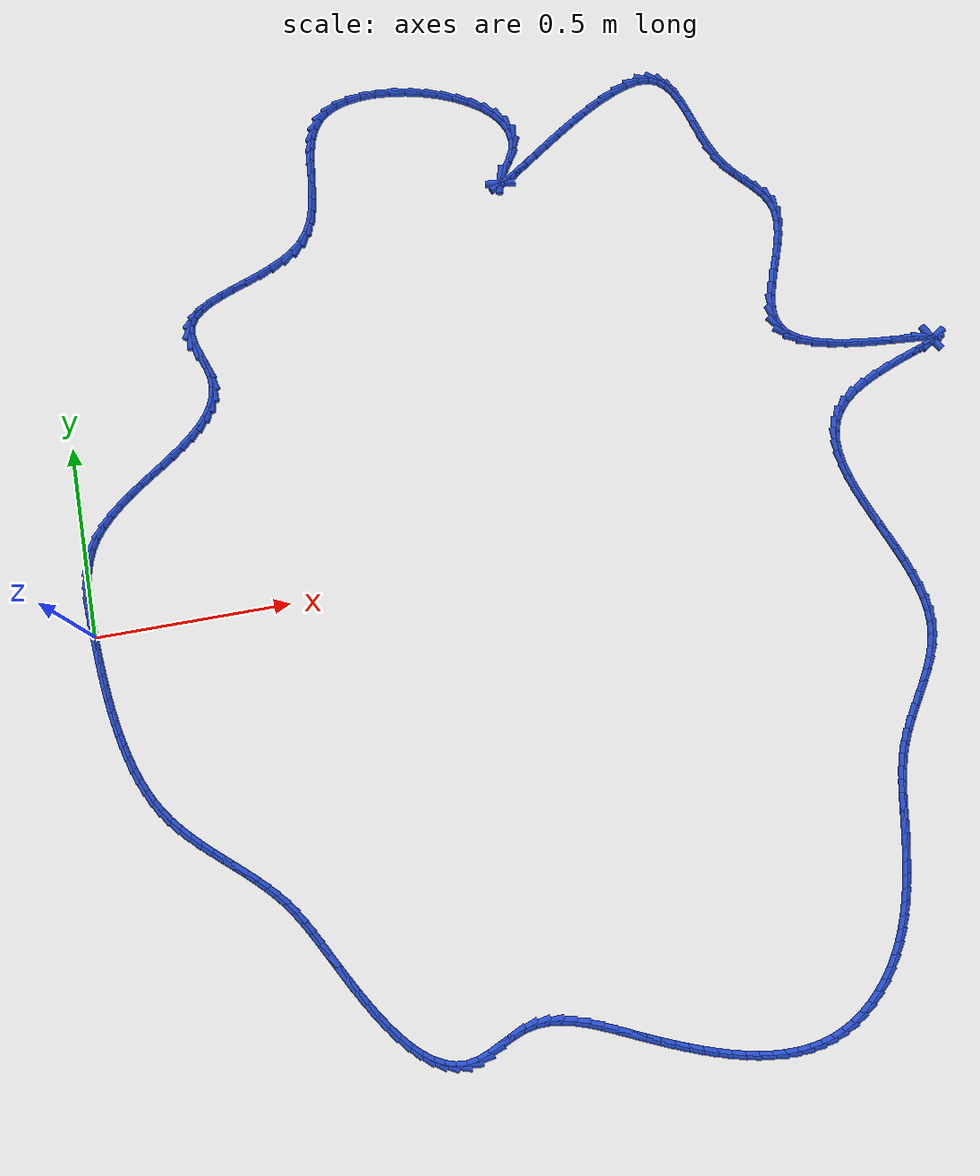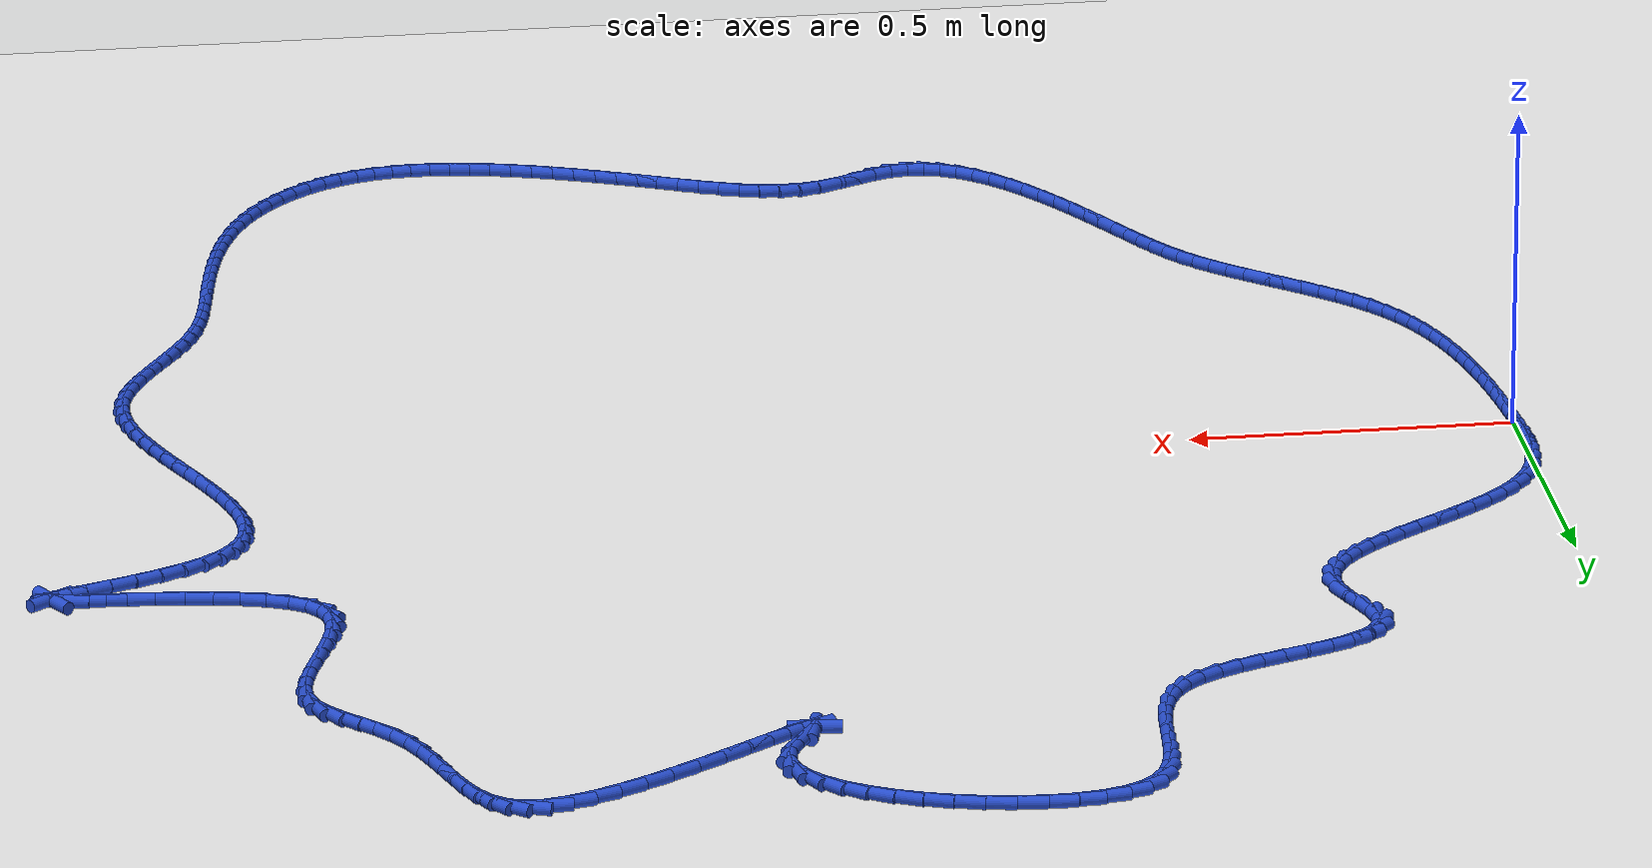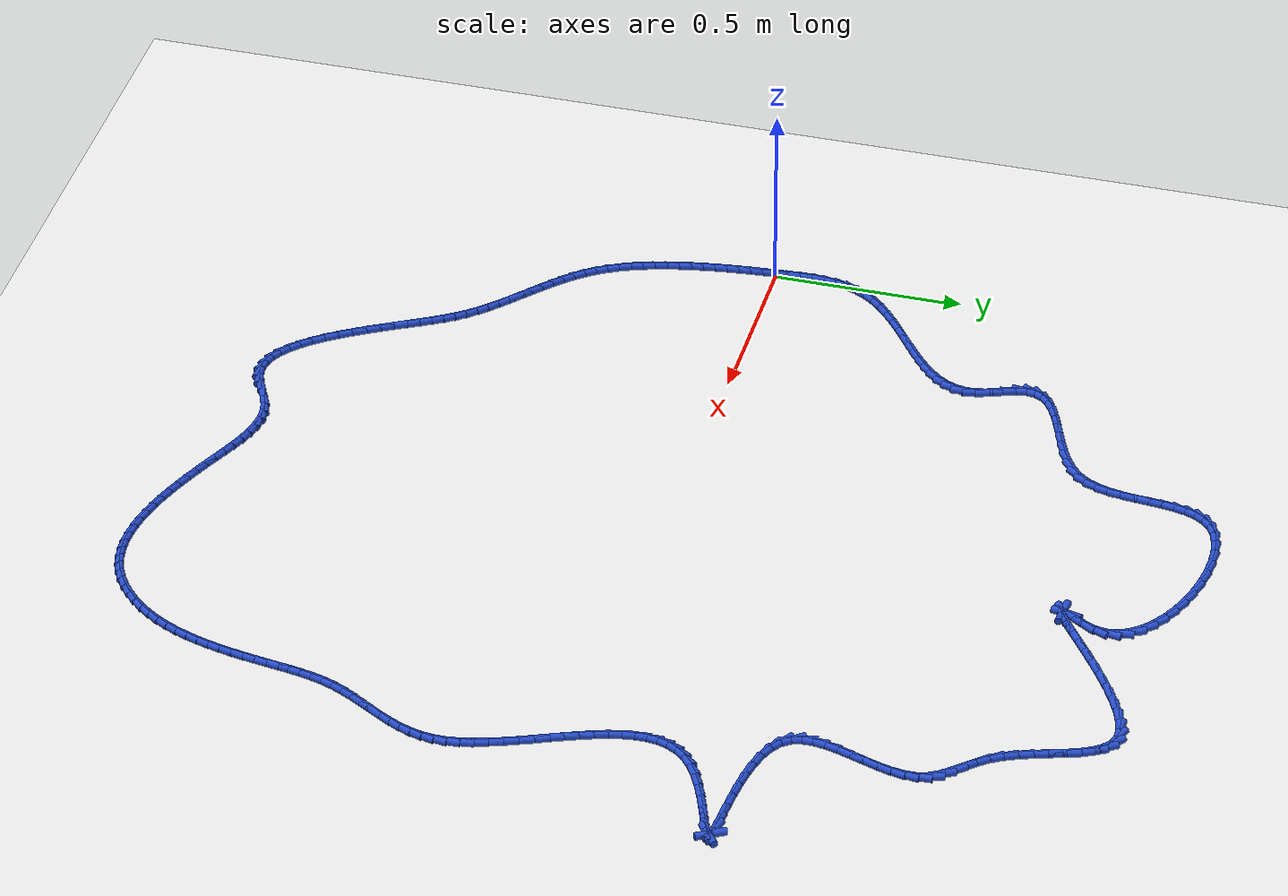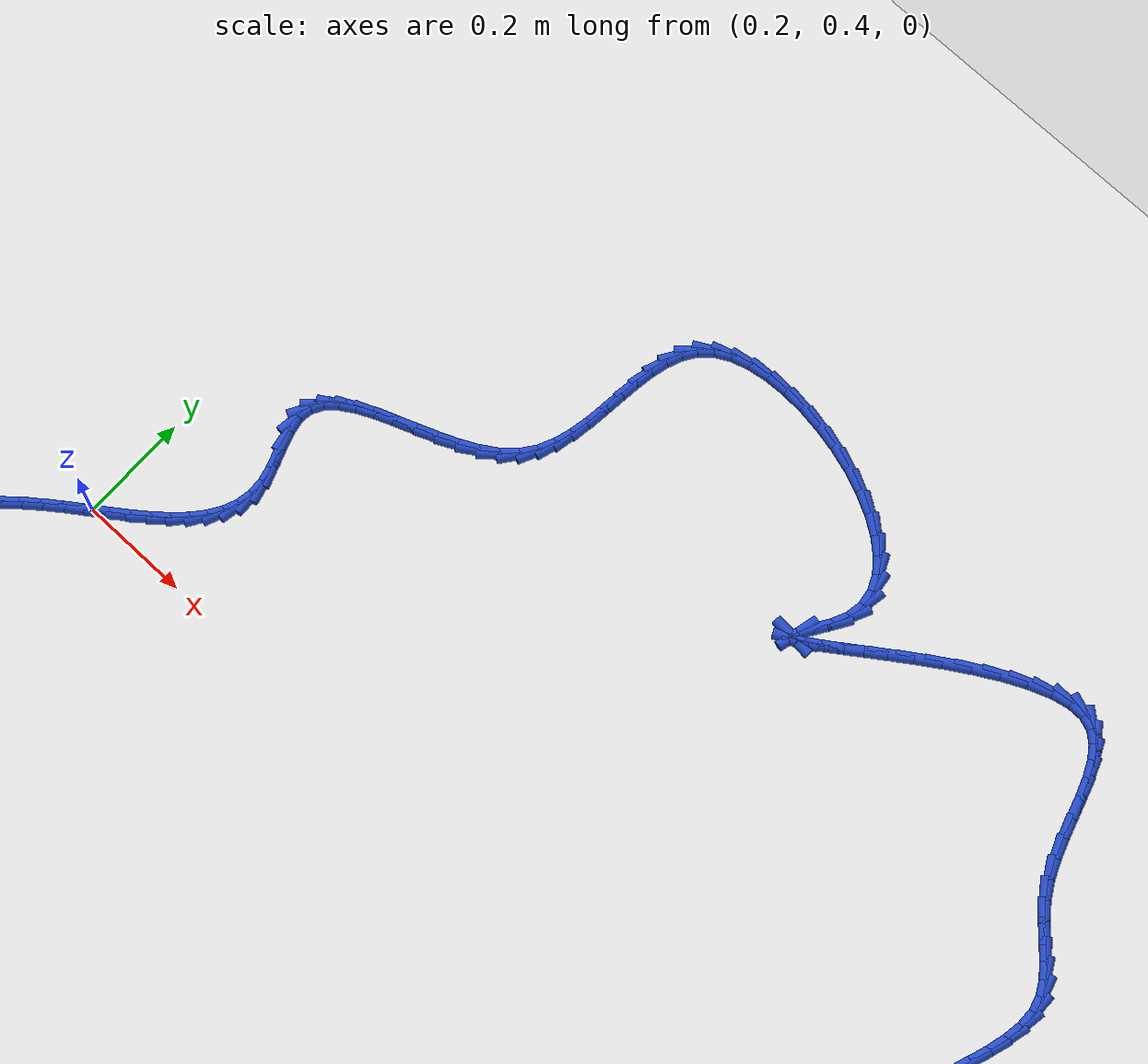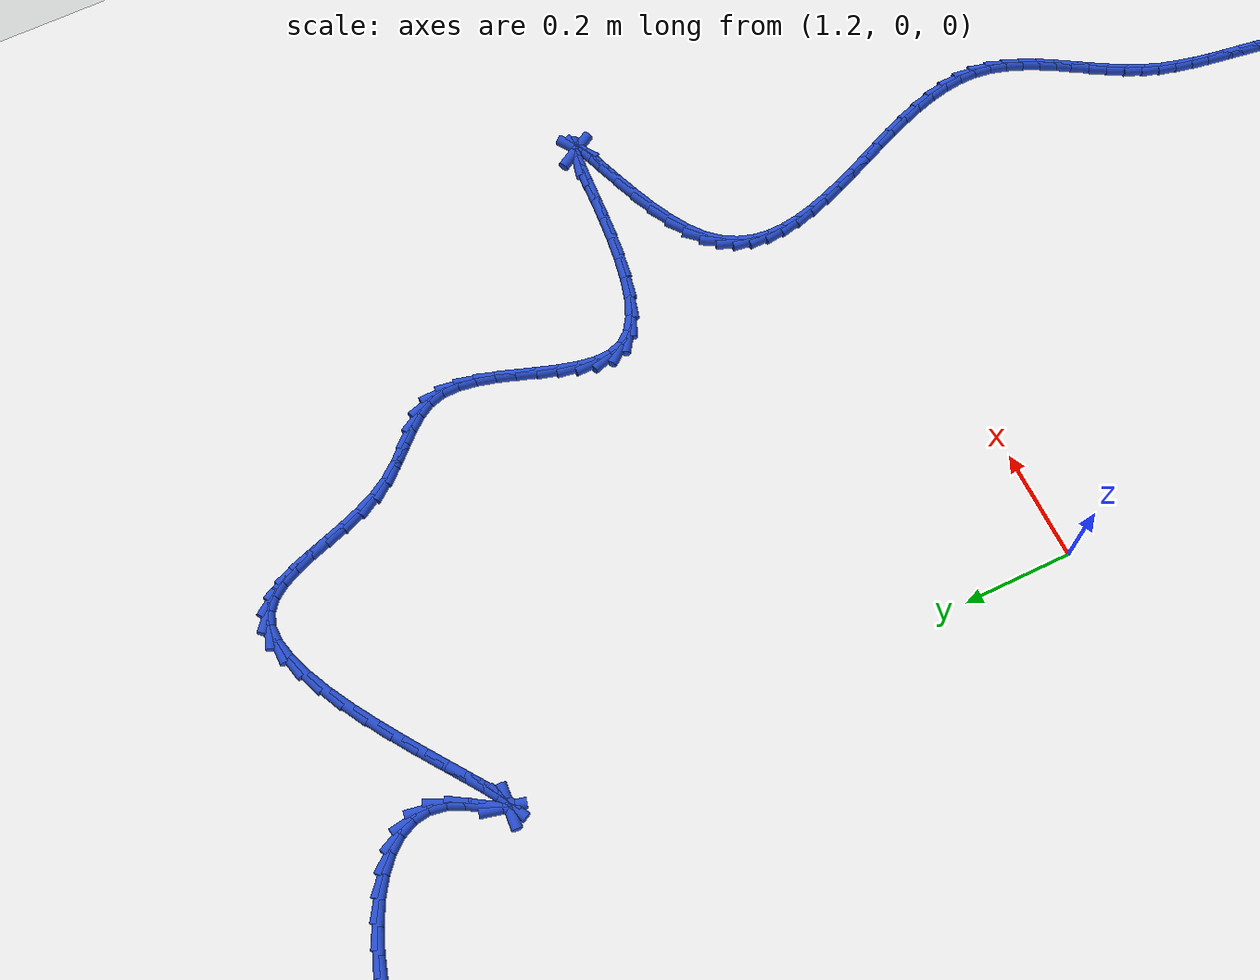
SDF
<sdf version="1.6">
 <world name="default">
  <light name="sun" type="directional">
   <pose>0 0 10 0 -0 0</pose>
   <diffuse>0.8 0.8 0.8 1</diffuse>
   <specular>0.2 0.2 0.2 1</specular>
   <attenuation>
    <range>1000</range>
    <constant>0.9</constant>
    <linear>0.01</linear>
    <quadratic>0.001</quadratic>
   </attenuation>
   <direction>-0.5 0.1 -0.9</direction>
  </light>
  <model name="ground_plane">
   <static>1</static>
   <link name="link">
    <collision name="collision">
     <geometry><plane><normal>0 0 1</normal><size>100 100</size></plane></geometry>
     <surface><friction><ode><mu>100</mu><mu2>50</mu2></ode></friction></surface>
    </collision>
    <visual name="visual">
     <cast_shadows>0</cast_shadows>
     <geometry><plane><normal>0 0 1</normal><size>100 100</size></plane></geometry>
     <material>
      <script><uri>file://media/materials/scripts/gazebo.material</uri><name>Gazebo/WhiteGlow</name></script>
     </material>
    </visual>
   </link>
  </model>
  <gravity>0 0 -9.8</gravity>
  <magnetic_field>6e-06 2.3e-05 -4.2e-05</magnetic_field>
  <atmosphere type="adiabatic"/>
  <physics name="default_physics" default="0" type="ode">
   <max_step_size>0.001</max_step_size>
   <real_time_factor>1</real_time_factor>
   <real_time_update_rate>1000</real_time_update_rate>
  </physics>
  <scene><ambient>0.4 0.4 0.4 1</ambient><background>0.7 0.7 0.7 1</background><shadows>1</shadows></scene>
  <spherical_coordinates>
   <surface_model>EARTH_WGS84</surface_model>
   <latitude_deg>0</latitude_deg>
   <longitude_deg>0</longitude_deg>
   <elevation>0</elevation>
   <heading_deg>0</heading_deg>
  </spherical_coordinates>
  <model name="line">
   <link name="link_0">
    <pose>7.806255641895632e-18 -4.85722573273506e-17 0.01 0 1.57 -1.5054916479996248</pose>
    <collision name="collision">
     <geometry><cylinder><radius>0.01</radius><length>0.08</length></cylinder></geometry>
    </collision>
    <visual name="visual">
     <material>
      <script><name>Gazebo/Blue</name><uri>file://media/materials/scripts/gazebo.material</uri></script>
     </material>
     <geometry><cylinder><radius>0.01</radius><length>0.08</length></cylinder></geometry>
    </visual>
   </link>
   <link name="link_1">
    <pose>-0.002153279578694225 0.03292593603509368 0.01 0 1.57 -1.528168202188111</pose>
    <collision name="collision">
     <geometry><cylinder><radius>0.01</radius><length>0.08</length></cylinder></geometry>
    </collision>
    <visual name="visual">
     <material>
      <script><name>Gazebo/Blue</name><uri>file://media/materials/scripts/gazebo.material</uri></script>
     </material>
     <geometry><cylinder><radius>0.01</radius><length>0.08</length></cylinder></geometry>
    </visual>
   </link>
   <link name="link_2">
    <pose>-0.003565207728112422 0.06602785705789568 0.01 0 1.57 -1.5683758969438606</pose>
    <collision name="collision">
     <geometry><cylinder><radius>0.01</radius><length>0.08</length></cylinder></geometry>
    </collision>
    <visual name="visual">
     <material>
      <script><name>Gazebo/Blue</name><uri>file://media/materials/scripts/gazebo.material</uri></script>
     </material>
     <geometry><cylinder><radius>0.01</radius><length>0.08</length></cylinder></geometry>
    </visual>
   </link>
   <link name="link_3">
    <pose>-0.0036450373039377845 0.09900936234621759 0.01 0 1.57 1.5142610973654411</pose>
    <collision name="collision">
     <geometry><cylinder><radius>0.01</radius><length>0.08</length></cylinder></geometry>
    </collision>
    <visual name="visual">
     <material>
      <script><name>Gazebo/Blue</name><uri>file://media/materials/scripts/gazebo.material</uri></script>
     </material>
     <geometry><cylinder><radius>0.01</radius><length>0.08</length></cylinder></geometry>
    </visual>
   </link>
   <link name="link_4">
    <pose>-0.001802021161853515 0.13157405117787097 0.01 0 1.57 1.4348609604948583</pose>
    <collision name="collision">
     <geometry><cylinder><radius>0.01</radius><length>0.08</length></cylinder></geometry>
    </collision>
    <visual name="visual">
     <material>
      <script><name>Gazebo/Blue</name><uri>file://media/materials/scripts/gazebo.material</uri></script>
     </material>
     <geometry><cylinder><radius>0.01</radius><length>0.08</length></cylinder></geometry>
    </visual>
   </link>
   <link name="link_5">
    <pose>0.002554587842457188 0.1634255228306674 0.01 0 1.57 1.3334462719967795</pose>
    <collision name="collision">
     <geometry><cylinder><radius>0.01</radius><length>0.08</length></cylinder></geometry>
    </collision>
    <visual name="visual">
     <material>
      <script><name>Gazebo/Blue</name><uri>file://media/materials/scripts/gazebo.material</uri></script>
     </material>
     <geometry><cylinder><radius>0.01</radius><length>0.08</length></cylinder></geometry>
    </visual>
   </link>
   <link name="link_6">
    <pose>0.010015536853311118 0.19426737658241858 0.01 0 1.57 1.2096502299227245</pose>
    <collision name="collision">
     <geometry><cylinder><radius>0.01</radius><length>0.08</length></cylinder></geometry>
    </collision>
    <visual name="visual">
     <material>
      <script><name>Gazebo/Blue</name><uri>file://media/materials/scripts/gazebo.material</uri></script>
     </material>
     <geometry><cylinder><radius>0.01</radius><length>0.08</length></cylinder></geometry>
    </visual>
   </link>
   <link name="link_7">
    <pose>0.021171573015025077 0.223803211710936 0.01 0 1.57 1.0664736958915768</pose>
    <collision name="collision">
     <geometry><cylinder><radius>0.01</radius><length>0.08</length></cylinder></geometry>
    </collision>
    <visual name="visual">
     <material>
      <script><name>Gazebo/Blue</name><uri>file://media/materials/scripts/gazebo.material</uri></script>
     </material>
     <geometry><cylinder><radius>0.01</radius><length>0.08</length></cylinder></geometry>
    </visual>
   </link>
   <link name="link_8">
    <pose>0.036593331610565424 0.25174479866111715 0.01 0 1.57 0.9284972561108572</pose>
    <collision name="collision">
     <geometry><cylinder><radius>0.01</radius><length>0.08</length></cylinder></geometry>
    </collision>
    <visual name="visual">
     <material>
      <script><name>Gazebo/Blue</name><uri>file://media/materials/scripts/gazebo.material</uri></script>
     </material>
     <geometry><cylinder><radius>0.01</radius><length>0.08</length></cylinder></geometry>
    </visual>
   </link>
   <link name="link_9">
    <pose>0.056266545943471996 0.27804154534559256 0.01 0 1.57 0.8190971684627749</pose>
    <collision name="collision">
     <geometry><cylinder><radius>0.01</radius><length>0.08</length></cylinder></geometry>
    </collision>
    <visual name="visual">
     <material>
      <script><name>Gazebo/Blue</name><uri>file://media/materials/scripts/gazebo.material</uri></script>
     </material>
     <geometry><cylinder><radius>0.01</radius><length>0.08</length></cylinder></geometry>
    </visual>
   </link>
   <link name="link_10">
    <pose>0.07951474358143529 0.30291190457634526 0.01 0 1.57 0.7365466639839479</pose>
    <collision name="collision">
     <geometry><cylinder><radius>0.01</radius><length>0.08</length></cylinder></geometry>
    </collision>
    <visual name="visual">
     <material>
      <script><name>Gazebo/Blue</name><uri>file://media/materials/scripts/gazebo.material</uri></script>
     </material>
     <geometry><cylinder><radius>0.01</radius><length>0.08</length></cylinder></geometry>
    </visual>
   </link>
   <link name="link_11">
    <pose>0.10562580476078533 0.3265888121759374 0.01 0 1.57 0.677044114920811</pose>
    <collision name="collision">
     <geometry><cylinder><radius>0.01</radius><length>0.08</length></cylinder></geometry>
    </collision>
    <visual name="visual">
     <material>
      <script><name>Gazebo/Blue</name><uri>file://media/materials/scripts/gazebo.material</uri></script>
     </material>
     <geometry><cylinder><radius>0.01</radius><length>0.08</length></cylinder></geometry>
    </visual>
   </link>
   <link name="link_12">
    <pose>0.1338876097178522 0.3493052039669312 0.01 0 1.57 0.6372986058783257</pose>
    <collision name="collision">
     <geometry><cylinder><radius>0.01</radius><length>0.08</length></cylinder></geometry>
    </collision>
    <visual name="visual">
     <material>
      <script><name>Gazebo/Blue</name><uri>file://media/materials/scripts/gazebo.material</uri></script>
     </material>
     <geometry><cylinder><radius>0.01</radius><length>0.08</length></cylinder></geometry>
    </visual>
   </link>
   <link name="link_13">
    <pose>0.16358803868896593 0.37129401577188886 0.01 0 1.57 0.6150211247521259</pose>
    <collision name="collision">
     <geometry><cylinder><radius>0.01</radius><length>0.08</length></cylinder></geometry>
    </collision>
    <visual name="visual">
     <material>
      <script><name>Gazebo/Blue</name><uri>file://media/materials/scripts/gazebo.material</uri></script>
     </material>
     <geometry><cylinder><radius>0.01</radius><length>0.08</length></cylinder></geometry>
    </visual>
   </link>
   <link name="link_14">
    <pose>0.19401497191045652 0.3927881834133726 0.01 0 1.57 0.6090381894384264</pose>
    <collision name="collision">
     <geometry><cylinder><radius>0.01</radius><length>0.08</length></cylinder></geometry>
    </collision>
    <visual name="visual">
     <material>
      <script><name>Gazebo/Blue</name><uri>file://media/materials/scripts/gazebo.material</uri></script>
     </material>
     <geometry><cylinder><radius>0.01</radius><length>0.08</length></cylinder></geometry>
    </visual>
   </link>
   <link name="link_15">
    <pose>0.22445628961865413 0.4140206427139447 0.01 0 1.57 0.6193198782790311</pose>
    <collision name="collision">
     <geometry><cylinder><radius>0.01</radius><length>0.08</length></cylinder></geometry>
    </collision>
    <visual name="visual">
     <material>
      <script><name>Gazebo/Blue</name><uri>file://media/materials/scripts/gazebo.material</uri></script>
     </material>
     <geometry><cylinder><radius>0.01</radius><length>0.08</length></cylinder></geometry>
    </visual>
   </link>
   <link name="link_16">
    <pose>0.2541998720498886 0.43522432949616713 0.01 0 1.57 0.6470504498278268</pose>
    <collision name="collision">
     <geometry><cylinder><radius>0.01</radius><length>0.08</length></cylinder></geometry>
    </collision>
    <visual name="visual">
     <material>
      <script><name>Gazebo/Blue</name><uri>file://media/materials/scripts/gazebo.material</uri></script>
     </material>
     <geometry><cylinder><radius>0.01</radius><length>0.08</length></cylinder></geometry>
    </visual>
   </link>
   <link name="link_17">
    <pose>0.2825335994404902 0.45663217958260244 0.01 0 1.57 0.6947792988689172</pose>
    <collision name="collision">
     <geometry><cylinder><radius>0.01</radius><length>0.08</length></cylinder></geometry>
    </collision>
    <visual name="visual">
     <material>
      <script><name>Gazebo/Blue</name><uri>file://media/materials/scripts/gazebo.material</uri></script>
     </material>
     <geometry><cylinder><radius>0.01</radius><length>0.08</length></cylinder></geometry>
    </visual>
   </link>
   <link name="link_18">
    <pose>0.30874535202678877 0.47847712879581267 0.01 0 1.57 0.7666027263242723</pose>
    <collision name="collision">
     <geometry><cylinder><radius>0.01</radius><length>0.08</length></cylinder></geometry>
    </collision>
    <visual name="visual">
     <material>
      <script><name>Gazebo/Blue</name><uri>file://media/materials/scripts/gazebo.material</uri></script>
     </material>
     <geometry><cylinder><radius>0.01</radius><length>0.08</length></cylinder></geometry>
    </visual>
   </link>
   <link name="link_19">
    <pose>0.3321230100451146 0.5009921129583602 0.01 0 1.57 0.8681351243195626</pose>
    <collision name="collision">
     <geometry><cylinder><radius>0.01</radius><length>0.08</length></cylinder></geometry>
    </collision>
    <visual name="visual">
     <material>
      <script><name>Gazebo/Blue</name><uri>file://media/materials/scripts/gazebo.material</uri></script>
     </material>
     <geometry><cylinder><radius>0.01</radius><length>0.08</length></cylinder></geometry>
    </visual>
   </link>
   <link name="link_20">
    <pose>0.35195445373179746 0.5244100678928072 0.01 0 1.57 1.0055781046518903</pose>
    <collision name="collision">
     <geometry><cylinder><radius>0.01</radius><length>0.08</length></cylinder></geometry>
    </collision>
    <visual name="visual">
     <material>
      <script><name>Gazebo/Blue</name><uri>file://media/materials/scripts/gazebo.material</uri></script>
     </material>
     <geometry><cylinder><radius>0.01</radius><length>0.08</length></cylinder></geometry>
    </visual>
   </link>
   <link name="link_21">
    <pose>0.36752756332316755 0.5489639294217157 0.01 0 1.57 1.1825465702987052</pose>
    <collision name="collision">
     <geometry><cylinder><radius>0.01</radius><length>0.08</length></cylinder></geometry>
    </collision>
    <visual name="visual">
     <material>
      <script><name>Gazebo/Blue</name><uri>file://media/materials/scripts/gazebo.material</uri></script>
     </material>
     <geometry><cylinder><radius>0.01</radius><length>0.08</length></cylinder></geometry>
    </visual>
   </link>
   <link name="link_22">
    <pose>0.3781302190555547 0.5748866333676479 0.01 0 1.57 1.3939115740549082</pose>
    <collision name="collision">
     <geometry><cylinder><radius>0.01</radius><length>0.08</length></cylinder></geometry>
    </collision>
    <visual name="visual">
     <material>
      <script><name>Gazebo/Blue</name><uri>file://media/materials/scripts/gazebo.material</uri></script>
     </material>
     <geometry><cylinder><radius>0.01</radius><length>0.08</length></cylinder></geometry>
    </visual>
   </link>
   <link name="link_23">
    <pose>0.3830503011652894 0.6024111155531664 0.01 0 1.57 -1.5206119438942363</pose>
    <collision name="collision">
     <geometry><cylinder><radius>0.01</radius><length>0.08</length></cylinder></geometry>
    </collision>
    <visual name="visual">
     <material>
      <script><name>Gazebo/Blue</name><uri>file://media/materials/scripts/gazebo.material</uri></script>
     </material>
     <geometry><cylinder><radius>0.01</radius><length>0.08</length></cylinder></geometry>
    </visual>
   </link>
   <link name="link_24">
    <pose>0.3815756898887013 0.6317703118008332 0.01 0 1.57 -1.3179037018304514</pose>
    <collision name="collision">
     <geometry><cylinder><radius>0.01</radius><length>0.08</length></cylinder></geometry>
    </collision>
    <visual name="visual">
     <material>
      <script><name>Gazebo/Blue</name><uri>file://media/materials/scripts/gazebo.material</uri></script>
     </material>
     <geometry><cylinder><radius>0.01</radius><length>0.08</length></cylinder></geometry>
    </visual>
   </link>
   <link name="link_25">
    <pose>0.37350186189091855 0.6630127015235091 0.01 0 1.57 -1.2231471986598406</pose>
    <collision name="collision">
     <geometry><cylinder><radius>0.01</radius><length>0.08</length></cylinder></geometry>
    </collision>
    <visual name="visual">
     <material>
      <script><name>Gazebo/Blue</name><uri>file://media/materials/scripts/gazebo.material</uri></script>
     </material>
     <geometry><cylinder><radius>0.01</radius><length>0.08</length></cylinder></geometry>
    </visual>
   </link>
   <link name="link_26">
    <pose>0.3619138615483157 0.6949913620093348 0.01 0 1.57 -1.2391776412990685</pose>
    <collision name="collision">
     <geometry><cylinder><radius>0.01</radius><length>0.08</length></cylinder></geometry>
    </collision>
    <visual name="visual">
     <material>
      <script><name>Gazebo/Blue</name><uri>file://media/materials/scripts/gazebo.material</uri></script>
     </material>
     <geometry><cylinder><radius>0.01</radius><length>0.08</length></cylinder></geometry>
    </visual>
   </link>
   <link name="link_27">
    <pose>0.3512079826000164 0.7260828732033762 0.01 0 1.57 -1.3832395769975614</pose>
    <collision name="collision">
     <geometry><cylinder><radius>0.01</radius><length>0.08</length></cylinder></geometry>
    </collision>
    <visual name="visual">
     <material>
      <script><name>Gazebo/Blue</name><uri>file://media/materials/scripts/gazebo.material</uri></script>
     </material>
     <geometry><cylinder><radius>0.01</radius><length>0.08</length></cylinder></geometry>
    </visual>
   </link>
   <link name="link_28">
    <pose>0.34578391400248076 0.7546625812563622 0.01 0 1.57 1.43109762839957</pose>
    <collision name="collision">
     <geometry><cylinder><radius>0.01</radius><length>0.08</length></cylinder></geometry>
    </collision>
    <visual name="visual">
     <material>
      <script><name>Gazebo/Blue</name><uri>file://media/materials/scripts/gazebo.material</uri></script>
     </material>
     <geometry><cylinder><radius>0.01</radius><length>0.08</length></cylinder></geometry>
    </visual>
   </link>
   <link name="link_29">
    <pose>0.3492647476257447 0.77941700260853 0.01 0 1.57 1.0473393882004238</pose>
    <collision name="collision">
     <geometry><cylinder><radius>0.01</radius><length>0.08</length></cylinder></geometry>
    </collision>
    <visual name="visual">
     <material>
      <script><name>Gazebo/Blue</name><uri>file://media/materials/scripts/gazebo.material</uri></script>
     </material>
     <geometry><cylinder><radius>0.01</radius><length>0.08</length></cylinder></geometry>
    </visual>
   </link>
   <link name="link_30">
    <pose>0.3614665502316619 0.8005580690355452 0.01 0 1.57 0.7492100019741645</pose>
    <collision name="collision">
     <geometry><cylinder><radius>0.01</radius><length>0.08</length></cylinder></geometry>
    </collision>
    <visual name="visual">
     <material>
      <script><name>Gazebo/Blue</name><uri>file://media/materials/scripts/gazebo.material</uri></script>
     </material>
     <geometry><cylinder><radius>0.01</radius><length>0.08</length></cylinder></geometry>
    </visual>
   </link>
   <link name="link_31">
    <pose>0.3810406773047011 0.8187643938802767 0.01 0 1.57 0.5572461036282345</pose>
    <collision name="collision">
     <geometry><cylinder><radius>0.01</radius><length>0.08</length></cylinder></geometry>
    </collision>
    <visual name="visual">
     <material>
      <script><name>Gazebo/Blue</name><uri>file://media/materials/scripts/gazebo.material</uri></script>
     </material>
     <geometry><cylinder><radius>0.01</radius><length>0.08</length></cylinder></geometry>
    </visual>
   </link>
   <link name="link_32">
    <pose>0.40663818812882147 0.8347147091684993 0.01 0 1.57 0.44328282518599665</pose>
    <collision name="collision">
     <geometry><cylinder><radius>0.01</radius><length>0.08</length></cylinder></geometry>
    </collision>
    <visual name="visual">
     <material>
      <script><name>Gazebo/Blue</name><uri>file://media/materials/scripts/gazebo.material</uri></script>
     </material>
     <geometry><cylinder><radius>0.01</radius><length>0.08</length></cylinder></geometry>
    </visual>
   </link>
   <link name="link_33">
    <pose>0.4369101419879813 0.8490877469259875 0.01 0 1.57 0.3814171817636546</pose>
    <collision name="collision">
     <geometry><cylinder><radius>0.01</radius><length>0.08</length></cylinder></geometry>
    </collision>
    <visual name="visual">
     <material>
      <script><name>Gazebo/Blue</name><uri>file://media/materials/scripts/gazebo.material</uri></script>
     </material>
     <geometry><cylinder><radius>0.01</radius><length>0.08</length></cylinder></geometry>
    </visual>
   </link>
   <link name="link_34">
    <pose>0.4705075981661396 0.8625622391785156 0.01 0 1.57 0.3566599593140726</pose>
    <collision name="collision">
     <geometry><cylinder><radius>0.01</radius><length>0.08</length></cylinder></geometry>
    </collision>
    <visual name="visual">
     <material>
      <script><name>Gazebo/Blue</name><uri>file://media/materials/scripts/gazebo.material</uri></script>
     </material>
     <geometry><cylinder><radius>0.01</radius><length>0.08</length></cylinder></geometry>
    </visual>
   </link>
   <link name="link_35">
    <pose>0.506081615947255 0.8758169179518586 0.01 0 1.57 0.36210807143996954</pose>
    <collision name="collision">
     <geometry><cylinder><radius>0.01</radius><length>0.08</length></cylinder></geometry>
    </collision>
    <visual name="visual">
     <material>
      <script><name>Gazebo/Blue</name><uri>file://media/materials/scripts/gazebo.material</uri></script>
     </material>
     <geometry><cylinder><radius>0.01</radius><length>0.08</length></cylinder></geometry>
    </visual>
   </link>
   <link name="link_36">
    <pose>0.542283254615286 0.8895305152717905 0.01 0 1.57 0.3964178140099533</pose>
    <collision name="collision">
     <geometry><cylinder><radius>0.01</radius><length>0.08</length></cylinder></geometry>
    </collision>
    <visual name="visual">
     <material>
      <script><name>Gazebo/Blue</name><uri>file://media/materials/scripts/gazebo.material</uri></script>
     </material>
     <geometry><cylinder><radius>0.01</radius><length>0.08</length></cylinder></geometry>
    </visual>
   </link>
   <link name="link_37">
    <pose>0.5777635734541913 0.9043817631640856 0.01 0 1.57 0.46275170157153556</pose>
    <collision name="collision">
     <geometry><cylinder><radius>0.01</radius><length>0.08</length></cylinder></geometry>
    </collision>
    <visual name="visual">
     <material>
      <script><name>Gazebo/Blue</name><uri>file://media/materials/scripts/gazebo.material</uri></script>
     </material>
     <geometry><cylinder><radius>0.01</radius><length>0.08</length></cylinder></geometry>
    </visual>
   </link>
   <link name="link_38">
    <pose>0.61117363174793 0.9210493936545189 0.01 0 1.57 0.5685700040137551</pose>
    <collision name="collision">
     <geometry><cylinder><radius>0.01</radius><length>0.08</length></cylinder></geometry>
    </collision>
    <visual name="visual">
     <material>
      <script><name>Gazebo/Blue</name><uri>file://media/materials/scripts/gazebo.material</uri></script>
     </material>
     <geometry><cylinder><radius>0.01</radius><length>0.08</length></cylinder></geometry>
    </visual>
   </link>
   <link name="link_39">
    <pose>0.6411644887804606 0.940212138768865 0.01 0 1.57 0.7247877709195721</pose>
    <collision name="collision">
     <geometry><cylinder><radius>0.01</radius><length>0.08</length></cylinder></geometry>
    </collision>
    <visual name="visual">
     <material>
      <script><name>Gazebo/Blue</name><uri>file://media/materials/scripts/gazebo.material</uri></script>
     </material>
     <geometry><cylinder><radius>0.01</radius><length>0.08</length></cylinder></geometry>
    </visual>
   </link>
   <link name="link_40">
    <pose>0.6663872038357417 0.9625487305328979 0.01 0 1.57 0.9323769082939156</pose>
    <collision name="collision">
     <geometry><cylinder><radius>0.01</radius><length>0.08</length></cylinder></geometry>
    </collision>
    <visual name="visual">
     <material>
      <script><name>Gazebo/Blue</name><uri>file://media/materials/scripts/gazebo.material</uri></script>
     </material>
     <geometry><cylinder><radius>0.01</radius><length>0.08</length></cylinder></geometry>
    </visual>
   </link>
   <link name="link_41">
    <pose>0.6857218123373217 0.98860299633883 0.01 0 1.57 1.1287810906283307</pose>
    <collision name="collision">
     <geometry><cylinder><radius>0.01</radius><length>0.08</length></cylinder></geometry>
    </collision>
    <visual name="visual">
     <material>
      <script><name>Gazebo/Blue</name><uri>file://media/materials/scripts/gazebo.material</uri></script>
     </material>
     <geometry><cylinder><radius>0.01</radius><length>0.08</length></cylinder></geometry>
    </visual>
   </link>
   <link name="link_42">
    <pose>0.6996281199836105 1.0179880188714803 0.01 0 1.57 1.2786721919331157</pose>
    <collision name="collision">
     <geometry><cylinder><radius>0.01</radius><length>0.08</length></cylinder></geometry>
    </collision>
    <visual name="visual">
     <material>
      <script><name>Gazebo/Blue</name><uri>file://media/materials/scripts/gazebo.material</uri></script>
     </material>
     <geometry><cylinder><radius>0.01</radius><length>0.08</length></cylinder></geometry>
    </visual>
   </link>
   <link name="link_43">
    <pose>0.7092322436329972 1.0499243138738164 0.01 0 1.57 1.3822863222796995</pose>
    <collision name="collision">
     <geometry><cylinder><radius>0.01</radius><length>0.08</length></cylinder></geometry>
    </collision>
    <visual name="visual">
     <material>
      <script><name>Gazebo/Blue</name><uri>file://media/materials/scripts/gazebo.material</uri></script>
     </material>
     <geometry><cylinder><radius>0.01</radius><length>0.08</length></cylinder></geometry>
    </visual>
   </link>
   <link name="link_44">
    <pose>0.7156626454405246 1.0836310153230637 0.01 0 1.57 1.4450762394214134</pose>
    <collision name="collision">
     <geometry><cylinder><radius>0.01</radius><length>0.08</length></cylinder></geometry>
    </collision>
    <visual name="visual">
     <material>
      <script><name>Gazebo/Blue</name><uri>file://media/materials/scripts/gazebo.material</uri></script>
     </material>
     <geometry><cylinder><radius>0.01</radius><length>0.08</length></cylinder></geometry>
    </visual>
   </link>
   <link name="link_45">
    <pose>0.720047787561235 1.118327257196448 0.01 0 1.57 1.471755927799328</pose>
    <collision name="collision">
     <geometry><cylinder><radius>0.01</radius><length>0.08</length></cylinder></geometry>
    </collision>
    <visual name="visual">
     <material>
      <script><name>Gazebo/Blue</name><uri>file://media/materials/scripts/gazebo.material</uri></script>
     </material>
     <geometry><cylinder><radius>0.01</radius><length>0.08</length></cylinder></geometry>
    </visual>
   </link>
   <link name="link_46">
    <pose>0.7235161321501716 1.1532321734711946 0.01 0 1.57 1.4640173737341098</pose>
    <collision name="collision">
     <geometry><cylinder><radius>0.01</radius><length>0.08</length></cylinder></geometry>
    </collision>
    <visual name="visual">
     <material>
      <script><name>Gazebo/Blue</name><uri>file://media/materials/scripts/gazebo.material</uri></script>
     </material>
     <geometry><cylinder><radius>0.01</radius><length>0.08</length></cylinder></geometry>
    </visual>
   </link>
   <link name="link_47">
    <pose>0.7271961413623765 1.1875648981245277 0.01 0 1.57 1.4197367973958306</pose>
    <collision name="collision">
     <geometry><cylinder><radius>0.01</radius><length>0.08</length></cylinder></geometry>
    </collision>
    <visual name="visual">
     <material>
      <script><name>Gazebo/Blue</name><uri>file://media/materials/scripts/gazebo.material</uri></script>
     </material>
     <geometry><cylinder><radius>0.01</radius><length>0.08</length></cylinder></geometry>
    </visual>
   </link>
   <link name="link_48">
    <pose>0.7322162773528923 1.2205445651336737 0.01 0 1.57 1.332624558508975</pose>
    <collision name="collision">
     <geometry><cylinder><radius>0.01</radius><length>0.08</length></cylinder></geometry>
    </collision>
    <visual name="visual">
     <material>
      <script><name>Gazebo/Blue</name><uri>file://media/materials/scripts/gazebo.material</uri></script>
     </material>
     <geometry><cylinder><radius>0.01</radius><length>0.08</length></cylinder></geometry>
    </visual>
   </link>
   <link name="link_49">
    <pose>0.7397050022767621 1.2513903084758575 0.01 0 1.57 1.1929658197713058</pose>
    <collision name="collision">
     <geometry><cylinder><radius>0.01</radius><length>0.08</length></cylinder></geometry>
    </collision>
    <visual name="visual">
     <material>
      <script><name>Gazebo/Blue</name><uri>file://media/materials/scripts/gazebo.material</uri></script>
     </material>
     <geometry><cylinder><radius>0.01</radius><length>0.08</length></cylinder></geometry>
    </visual>
   </link>
   <link name="link_50">
    <pose>0.7507907782890281 1.2793212621283048 0.01 0 1.57 0.9927305503378063</pose>
    <collision name="collision">
     <geometry><cylinder><radius>0.01</radius><length>0.08</length></cylinder></geometry>
    </collision>
    <visual name="visual">
     <material>
      <script><name>Gazebo/Blue</name><uri>file://media/materials/scripts/gazebo.material</uri></script>
     </material>
     <geometry><cylinder><radius>0.01</radius><length>0.08</length></cylinder></geometry>
    </visual>
   </link>
   <link name="link_51">
    <pose>0.7666020675447331 1.3035565600682402 0.01 0 1.57 0.7397249864323698</pose>
    <collision name="collision">
     <geometry><cylinder><radius>0.01</radius><length>0.08</length></cylinder></geometry>
    </collision>
    <visual name="visual">
     <material>
      <script><name>Gazebo/Blue</name><uri>file://media/materials/scripts/gazebo.material</uri></script>
     </material>
     <geometry><cylinder><radius>0.01</radius><length>0.08</length></cylinder></geometry>
    </visual>
   </link>
   <link name="link_52">
    <pose>0.7882581621080893 1.323319594890137 0.01 0 1.57 0.4900271819980556</pose>
    <collision name="collision">
     <geometry><cylinder><radius>0.01</radius><length>0.08</length></cylinder></geometry>
    </collision>
    <visual name="visual">
     <material>
      <script><name>Gazebo/Blue</name><uri>file://media/materials/scripts/gazebo.material</uri></script>
     </material>
     <geometry><cylinder><radius>0.01</radius><length>0.08</length></cylinder></geometry>
    </visual>
   </link>
   <link name="link_53">
    <pose>0.8161242084082029 1.3381839866472875 0.01 0 1.57 0.2970957197492684</pose>
    <collision name="collision">
     <geometry><cylinder><radius>0.01</radius><length>0.08</length></cylinder></geometry>
    </collision>
    <visual name="visual">
     <material>
      <script><name>Gazebo/Blue</name><uri>file://media/materials/scripts/gazebo.material</uri></script>
     </material>
     <geometry><cylinder><radius>0.01</radius><length>0.08</length></cylinder></geometry>
    </visual>
   </link>
   <link name="link_54">
    <pose>0.8492610731573459 1.3483290667430914 0.01 0 1.57 0.15057838577999863</pose>
    <collision name="collision">
     <geometry><cylinder><radius>0.01</radius><length>0.08</length></cylinder></geometry>
    </collision>
    <visual name="visual">
     <material>
      <script><name>Gazebo/Blue</name><uri>file://media/materials/scripts/gazebo.material</uri></script>
     </material>
     <geometry><cylinder><radius>0.01</radius><length>0.08</length></cylinder></geometry>
    </visual>
   </link>
   <link name="link_55">
    <pose>0.8865999655675696 1.3539943799067367 0.01 0 1.57 0.03519712088303328</pose>
    <collision name="collision">
     <geometry><cylinder><radius>0.01</radius><length>0.08</length></cylinder></geometry>
    </collision>
    <visual name="visual">
     <material>
      <script><name>Gazebo/Blue</name><uri>file://media/materials/scripts/gazebo.material</uri></script>
     </material>
     <geometry><cylinder><radius>0.01</radius><length>0.08</length></cylinder></geometry>
    </visual>
   </link>
   <link name="link_56">
    <pose>0.9270720948509248 1.355419470867413 0.01 0 1.57 -0.06047609094073945</pose>
    <collision name="collision">
     <geometry><cylinder><radius>0.01</radius><length>0.08</length></cylinder></geometry>
    </collision>
    <visual name="visual">
     <material>
      <script><name>Gazebo/Blue</name><uri>file://media/materials/scripts/gazebo.material</uri></script>
     </material>
     <geometry><cylinder><radius>0.01</radius><length>0.08</length></cylinder></geometry>
    </visual>
   </link>
   <link name="link_57">
    <pose>0.9696086702194622 1.3528438843543087 0.01 0 1.57 -0.14454862027172444</pose>
    <collision name="collision">
     <geometry><cylinder><radius>0.01</radius><length>0.08</length></cylinder></geometry>
    </collision>
    <visual name="visual">
     <material>
      <script><name>Gazebo/Blue</name><uri>file://media/materials/scripts/gazebo.material</uri></script>
     </material>
     <geometry><cylinder><radius>0.01</radius><length>0.08</length></cylinder></geometry>
    </visual>
   </link>
   <link name="link_58">
    <pose>1.0131409008852335 1.3465071650966127 0.01 0 1.57 -0.22306609857474466</pose>
    <collision name="collision">
     <geometry><cylinder><radius>0.01</radius><length>0.08</length></cylinder></geometry>
    </collision>
    <visual name="visual">
     <material>
      <script><name>Gazebo/Blue</name><uri>file://media/materials/scripts/gazebo.material</uri></script>
     </material>
     <geometry><cylinder><radius>0.01</radius><length>0.08</length></cylinder></geometry>
    </visual>
   </link>
   <link name="link_59">
    <pose>1.0565999960602894 1.336648857823514 0.01 0 1.57 -0.3010805111296582</pose>
    <collision name="collision">
     <geometry><cylinder><radius>0.01</radius><length>0.08</length></cylinder></geometry>
    </collision>
    <visual name="visual">
     <material>
      <script><name>Gazebo/Blue</name><uri>file://media/materials/scripts/gazebo.material</uri></script>
     </material>
     <geometry><cylinder><radius>0.01</radius><length>0.08</length></cylinder></geometry>
    </visual>
   </link>
   <link name="link_60">
    <pose>1.0989171649566802 1.3235085072642012 0.01 0 1.57 -0.38351773801062394</pose>
    <collision name="collision">
     <geometry><cylinder><radius>0.01</radius><length>0.08</length></cylinder></geometry>
    </collision>
    <visual name="visual">
     <material>
      <script><name>Gazebo/Blue</name><uri>file://media/materials/scripts/gazebo.material</uri></script>
     </material>
     <geometry><cylinder><radius>0.01</radius><length>0.08</length></cylinder></geometry>
    </visual>
   </link>
   <link name="link_61">
    <pose>1.1390236167864578 1.307325658147863 0.01 0 1.57 -0.47600304385480163</pose>
    <collision name="collision">
     <geometry><cylinder><radius>0.01</radius><length>0.08</length></cylinder></geometry>
    </collision>
    <visual name="visual">
     <material>
      <script><name>Gazebo/Blue</name><uri>file://media/materials/scripts/gazebo.material</uri></script>
     </material>
     <geometry><cylinder><radius>0.01</radius><length>0.08</length></cylinder></geometry>
    </visual>
   </link>
   <link name="link_62">
    <pose>1.1758505607616736 1.2883398552036889 0.01 0 1.57 -0.5857991990873849</pose>
    <collision name="collision">
     <geometry><cylinder><radius>0.01</radius><length>0.08</length></cylinder></geometry>
    </collision>
    <visual name="visual">
     <material>
      <script><name>Gazebo/Blue</name><uri>file://media/materials/scripts/gazebo.material</uri></script>
     </material>
     <geometry><cylinder><radius>0.01</radius><length>0.08</length></cylinder></geometry>
    </visual>
   </link>
   <link name="link_63">
    <pose>1.208329206094377 1.2667906431608669 0.01 0 1.57 -0.7228803003452667</pose>
    <collision name="collision">
     <geometry><cylinder><radius>0.01</radius><length>0.08</length></cylinder></geometry>
    </collision>
    <visual name="visual">
     <material>
      <script><name>Gazebo/Blue</name><uri>file://media/materials/scripts/gazebo.material</uri></script>
     </material>
     <geometry><cylinder><radius>0.01</radius><length>0.08</length></cylinder></geometry>
    </visual>
   </link>
   <link name="link_64">
    <pose>1.2353907619966202 1.2429175667485863 0.01 0 1.57 -0.9005402769997615</pose>
    <collision name="collision">
     <geometry><cylinder><radius>0.01</radius><length>0.08</length></cylinder></geometry>
    </collision>
    <visual name="visual">
     <material>
      <script><name>Gazebo/Blue</name><uri>file://media/materials/scripts/gazebo.material</uri></script>
     </material>
     <geometry><cylinder><radius>0.01</radius><length>0.08</length></cylinder></geometry>
    </visual>
   </link>
   <link name="link_65">
    <pose>1.255966437680454 1.216960170696036 0.01 0 1.57 -1.132791951174022</pose>
    <collision name="collision">
     <geometry><cylinder><radius>0.01</radius><length>0.08</length></cylinder></geometry>
    </collision>
    <visual name="visual">
     <material>
      <script><name>Gazebo/Blue</name><uri>file://media/materials/scripts/gazebo.material</uri></script>
     </material>
     <geometry><cylinder><radius>0.01</radius><length>0.08</length></cylinder></geometry>
    </visual>
   </link>
   <link name="link_66">
    <pose>1.2689874423579295 1.1891579997324047 0.01 0 1.57 -1.4223576138626208</pose>
    <collision name="collision">
     <geometry><cylinder><radius>0.01</radius><length>0.08</length></cylinder></geometry>
    </collision>
    <visual name="visual">
     <material>
      <script><name>Gazebo/Blue</name><uri>file://media/materials/scripts/gazebo.material</uri></script>
     </material>
     <geometry><cylinder><radius>0.01</radius><length>0.08</length></cylinder></geometry>
    </visual>
   </link>
   <link name="link_67">
    <pose>1.273384985241097 1.1597505985868801 0.01 0 1.57 1.4004081107630555</pose>
    <collision name="collision">
     <geometry><cylinder><radius>0.01</radius><length>0.08</length></cylinder></geometry>
    </collision>
    <visual name="visual">
     <material>
      <script><name>Gazebo/Blue</name><uri>file://media/materials/scripts/gazebo.material</uri></script>
     </material>
     <geometry><cylinder><radius>0.01</radius><length>0.08</length></cylinder></geometry>
    </visual>
   </link>
   <link name="link_68">
    <pose>1.2680902755420087 1.1289775119886534 0.01 0 1.57 1.1302657393272562</pose>
    <collision name="collision">
     <geometry><cylinder><radius>0.01</radius><length>0.08</length></cylinder></geometry>
    </collision>
    <visual name="visual">
     <material>
      <script><name>Gazebo/Blue</name><uri>file://media/materials/scripts/gazebo.material</uri></script>
     </material>
     <geometry><cylinder><radius>0.01</radius><length>0.08</length></cylinder></geometry>
    </visual>
   </link>
   <link name="link_69">
    <pose>1.2533442007404147 1.0976979793979984 0.01 0 1.57 1.0071582033349646</pose>
    <collision name="collision">
     <geometry><cylinder><radius>0.01</radius><length>0.08</length></cylinder></geometry>
    </collision>
    <visual name="visual">
     <material>
      <script><name>Gazebo/Blue</name><uri>file://media/materials/scripts/gazebo.material</uri></script>
     </material>
     <geometry><cylinder><radius>0.01</radius><length>0.08</length></cylinder></geometry>
    </visual>
   </link>
   <link name="link_70">
    <pose>1.235679075652324 1.0697481273988851 0.01 0 1.57 1.019825382333706</pose>
    <collision name="collision">
     <geometry><cylinder><radius>0.01</radius><length>0.08</length></cylinder></geometry>
    </collision>
    <visual name="visual">
     <material>
      <script><name>Gazebo/Blue</name><uri>file://media/materials/scripts/gazebo.material</uri></script>
     </material>
     <geometry><cylinder><radius>0.01</radius><length>0.08</length></cylinder></geometry>
    </visual>
   </link>
   <link name="link_71">
    <pose>1.2234204404681743 1.049797283249335 0.01 0 1.57 1.3300005908872918</pose>
    <collision name="collision">
     <geometry><cylinder><radius>0.01</radius><length>0.08</length></cylinder></geometry>
    </collision>
    <visual name="visual">
     <material>
      <script><name>Gazebo/Blue</name><uri>file://media/materials/scripts/gazebo.material</uri></script>
     </material>
     <geometry><cylinder><radius>0.01</radius><length>0.08</length></cylinder></geometry>
    </visual>
   </link>
   <link name="link_72">
    <pose>1.221027924146676 1.0400541906435077 0.01 0 1.57 -0.08962997798281555</pose>
    <collision name="collision">
     <geometry><cylinder><radius>0.01</radius><length>0.08</length></cylinder></geometry>
    </collision>
    <visual name="visual">
     <material>
      <script><name>Gazebo/Blue</name><uri>file://media/materials/scripts/gazebo.material</uri></script>
     </material>
     <geometry><cylinder><radius>0.01</radius><length>0.08</length></cylinder></geometry>
    </visual>
   </link>
   <link name="link_73">
    <pose>1.2278039807345142 1.039445221241442 0.01 0 1.57 0.45170516217936424</pose>
    <collision name="collision">
     <geometry><cylinder><radius>0.01</radius><length>0.08</length></cylinder></geometry>
    </collision>
    <visual name="visual">
     <material>
      <script><name>Gazebo/Blue</name><uri>file://media/materials/scripts/gazebo.material</uri></script>
     </material>
     <geometry><cylinder><radius>0.01</radius><length>0.08</length></cylinder></geometry>
    </visual>
   </link>
   <link name="link_74">
    <pose>1.2426925044056536 1.0466685351495937 0.01 0 1.57 0.5598502319994845</pose>
    <collision name="collision">
     <geometry><cylinder><radius>0.01</radius><length>0.08</length></cylinder></geometry>
    </collision>
    <visual name="visual">
     <material>
      <script><name>Gazebo/Blue</name><uri>file://media/materials/scripts/gazebo.material</uri></script>
     </material>
     <geometry><cylinder><radius>0.01</radius><length>0.08</length></cylinder></geometry>
    </visual>
   </link>
   <link name="link_75">
    <pose>1.264637389334059 1.060422292474418 0.01 0 1.57 0.5966789095214345</pose>
    <collision name="collision">
     <geometry><cylinder><radius>0.01</radius><length>0.08</length></cylinder></geometry>
    </collision>
    <visual name="visual">
     <material>
      <script><name>Gazebo/Blue</name><uri>file://media/materials/scripts/gazebo.material</uri></script>
     </material>
     <geometry><cylinder><radius>0.01</radius><length>0.08</length></cylinder></geometry>
    </visual>
   </link>
   <link name="link_76">
    <pose>1.2925825296936941 1.0794046533223696 0.01 0 1.57 0.6084086066822725</pose>
    <collision name="collision">
     <geometry><cylinder><radius>0.01</radius><length>0.08</length></cylinder></geometry>
    </collision>
    <visual name="visual">
     <material>
      <script><name>Gazebo/Blue</name><uri>file://media/materials/scripts/gazebo.material</uri></script>
     </material>
     <geometry><cylinder><radius>0.01</radius><length>0.08</length></cylinder></geometry>
    </visual>
   </link>
   <link name="link_77">
    <pose>1.3254718196585236 1.1023137777999044 0.01 0 1.57 0.6068818676930715</pose>
    <collision name="collision">
     <geometry><cylinder><radius>0.01</radius><length>0.08</length></cylinder></geometry>
    </collision>
    <visual name="visual">
     <material>
      <script><name>Gazebo/Blue</name><uri>file://media/materials/scripts/gazebo.material</uri></script>
     </material>
     <geometry><cylinder><radius>0.01</radius><length>0.08</length></cylinder></geometry>
    </visual>
   </link>
   <link name="link_78">
    <pose>1.3622491534025123 1.1278478260134774 0.01 0 1.57 0.5958431550132711</pose>
    <collision name="collision">
     <geometry><cylinder><radius>0.01</radius><length>0.08</length></cylinder></geometry>
    </collision>
    <visual name="visual">
     <material>
      <script><name>Gazebo/Blue</name><uri>file://media/materials/scripts/gazebo.material</uri></script>
     </material>
     <geometry><cylinder><radius>0.01</radius><length>0.08</length></cylinder></geometry>
    </visual>
   </link>
   <link name="link_79">
    <pose>1.401858425099624 1.154704958069544 0.01 0 1.57 0.5760024215270412</pose>
    <collision name="collision">
     <geometry><cylinder><radius>0.01</radius><length>0.08</length></cylinder></geometry>
    </collision>
    <visual name="visual">
     <material>
      <script><name>Gazebo/Blue</name><uri>file://media/materials/scripts/gazebo.material</uri></script>
     </material>
     <geometry><cylinder><radius>0.01</radius><length>0.08</length></cylinder></geometry>
    </visual>
   </link>
   <link name="link_80">
    <pose>1.4432435289238235 1.181583334074559 0.01 0 1.57 0.5462471683541248</pose>
    <collision name="collision">
     <geometry><cylinder><radius>0.01</radius><length>0.08</length></cylinder></geometry>
    </collision>
    <visual name="visual">
     <material>
      <script><name>Gazebo/Blue</name><uri>file://media/materials/scripts/gazebo.material</uri></script>
     </material>
     <geometry><cylinder><radius>0.01</radius><length>0.08</length></cylinder></geometry>
    </visual>
   </link>
   <link name="link_81">
    <pose>1.485348359049075 1.2071811141349784 0.01 0 1.57 0.5036276831516681</pose>
    <collision name="collision">
     <geometry><cylinder><radius>0.01</radius><length>0.08</length></cylinder></geometry>
    </collision>
    <visual name="visual">
     <material>
      <script><name>Gazebo/Blue</name><uri>file://media/materials/scripts/gazebo.material</uri></script>
     </material>
     <geometry><cylinder><radius>0.01</radius><length>0.08</length></cylinder></geometry>
    </visual>
   </link>
   <link name="link_82">
    <pose>1.527116809649343 1.2301964583572567 0.01 0 1.57 0.4424877239583572</pose>
    <collision name="collision">
     <geometry><cylinder><radius>0.01</radius><length>0.08</length></cylinder></geometry>
    </collision>
    <visual name="visual">
     <material>
      <script><name>Gazebo/Blue</name><uri>file://media/materials/scripts/gazebo.material</uri></script>
     </material>
     <geometry><cylinder><radius>0.01</radius><length>0.08</length></cylinder></geometry>
    </visual>
   </link>
   <link name="link_83">
    <pose>1.5674927748985923 1.24932752684785 0.01 0 1.57 0.3523334688093177</pose>
    <collision name="collision">
     <geometry><cylinder><radius>0.01</radius><length>0.08</length></cylinder></geometry>
    </collision>
    <visual name="visual">
     <material>
      <script><name>Gazebo/Blue</name><uri>file://media/materials/scripts/gazebo.material</uri></script>
     </material>
     <geometry><cylinder><radius>0.01</radius><length>0.08</length></cylinder></geometry>
    </visual>
   </link>
   <link name="link_84">
    <pose>1.6054201489707869 1.2632724797132129 0.01 0 1.57 0.21333397487717423</pose>
    <collision name="collision">
     <geometry><cylinder><radius>0.01</radius><length>0.08</length></cylinder></geometry>
    </collision>
    <visual name="visual">
     <material>
      <script><name>Gazebo/Blue</name><uri>file://media/materials/scripts/gazebo.material</uri></script>
     </material>
     <geometry><cylinder><radius>0.01</radius><length>0.08</length></cylinder></geometry>
    </visual>
   </link>
   <link name="link_85">
    <pose>1.639842826039891 1.2707294770598008 0.01 0 1.57 -0.011144119289282977</pose>
    <collision name="collision">
     <geometry><cylinder><radius>0.01</radius><length>0.08</length></cylinder></geometry>
    </collision>
    <visual name="visual">
     <material>
      <script><name>Gazebo/Blue</name><uri>file://media/materials/scripts/gazebo.material</uri></script>
     </material>
     <geometry><cylinder><radius>0.01</radius><length>0.08</length></cylinder></geometry>
    </visual>
   </link>
   <link name="link_86">
    <pose>1.6697047002798702 1.2703966789940695 0.01 0 1.57 -0.35107430216440577</pose>
    <collision name="collision">
     <geometry><cylinder><radius>0.01</radius><length>0.08</length></cylinder></geometry>
    </collision>
    <visual name="visual">
     <material>
      <script><name>Gazebo/Blue</name><uri>file://media/materials/scripts/gazebo.material</uri></script>
     </material>
     <geometry><cylinder><radius>0.01</radius><length>0.08</length></cylinder></geometry>
    </visual>
   </link>
   <link name="link_87">
    <pose>1.6942783260812213 1.2613966764852742 0.01 0 1.57 -0.7002691836156041</pose>
    <collision name="collision">
     <geometry><cylinder><radius>0.01</radius><length>0.08</length></cylinder></geometry>
    </collision>
    <visual name="visual">
     <material>
      <script><name>Gazebo/Blue</name><uri>file://media/materials/scripts/gazebo.material</uri></script>
     </material>
     <geometry><cylinder><radius>0.01</radius><length>0.08</length></cylinder></geometry>
    </visual>
   </link>
   <link name="link_88">
    <pose>1.7141974320585887 1.2446098769992011 0.01 0 1.57 -0.9605348628066841</pose>
    <collision name="collision">
     <geometry><cylinder><radius>0.01</radius><length>0.08</length></cylinder></geometry>
    </collision>
    <visual name="visual">
     <material>
      <script><name>Gazebo/Blue</name><uri>file://media/materials/scripts/gazebo.material</uri></script>
     </material>
     <geometry><cylinder><radius>0.01</radius><length>0.08</length></cylinder></geometry>
    </visual>
   </link>
   <link name="link_89">
    <pose>1.7304480825580548 1.2213716933566092 0.01 0 1.57 -1.1244733069168174</pose>
    <collision name="collision">
     <geometry><cylinder><radius>0.01</radius><length>0.08</length></cylinder></geometry>
    </collision>
    <visual name="visual">
     <material>
      <script><name>Gazebo/Blue</name><uri>file://media/materials/scripts/gazebo.material</uri></script>
     </material>
     <geometry><cylinder><radius>0.01</radius><length>0.08</length></cylinder></geometry>
    </visual>
   </link>
   <link name="link_90">
    <pose>1.7440163424561237 1.1930175390632434 0.01 0 1.57 -1.216906699708312</pose>
    <collision name="collision">
     <geometry><cylinder><radius>0.01</radius><length>0.08</length></cylinder></geometry>
    </collision>
    <visual name="visual">
     <material>
      <script><name>Gazebo/Blue</name><uri>file://media/materials/scripts/gazebo.material</uri></script>
     </material>
     <geometry><cylinder><radius>0.01</radius><length>0.08</length></cylinder></geometry>
    </visual>
   </link>
   <link name="link_91">
    <pose>1.7558882766292991 1.1608828276248473 0.01 0 1.57 -1.2585739723093685</pose>
    <collision name="collision">
     <geometry><cylinder><radius>0.01</radius><length>0.08</length></cylinder></geometry>
    </collision>
    <visual name="visual">
     <material>
      <script><name>Gazebo/Blue</name><uri>file://media/materials/scripts/gazebo.material</uri></script>
     </material>
     <geometry><cylinder><radius>0.01</radius><length>0.08</length></cylinder></geometry>
    </visual>
   </link>
   <link name="link_92">
    <pose>1.7670499499540828 1.1263029725471656 0.01 0 1.57 -1.2606661836608997</pose>
    <collision name="collision">
     <geometry><cylinder><radius>0.01</radius><length>0.08</length></cylinder></geometry>
    </collision>
    <visual name="visual">
     <material>
      <script><name>Gazebo/Blue</name><uri>file://media/materials/scripts/gazebo.material</uri></script>
     </material>
     <geometry><cylinder><radius>0.01</radius><length>0.08</length></cylinder></geometry>
    </visual>
   </link>
   <link name="link_93">
    <pose>1.7784874273069806 1.0906133873359432 0.01 0 1.57 -1.2269306978500822</pose>
    <collision name="collision">
     <geometry><cylinder><radius>0.01</radius><length>0.08</length></cylinder></geometry>
    </collision>
    <visual name="visual">
     <material>
      <script><name>Gazebo/Blue</name><uri>file://media/materials/scripts/gazebo.material</uri></script>
     </material>
     <geometry><cylinder><radius>0.01</radius><length>0.08</length></cylinder></geometry>
    </visual>
   </link>
   <link name="link_94">
    <pose>1.7911867735644962 1.055149485496924 0.01 0 1.57 -1.155547205642037</pose>
    <collision name="collision">
     <geometry><cylinder><radius>0.01</radius><length>0.08</length></cylinder></geometry>
    </collision>
    <visual name="visual">
     <material>
      <script><name>Gazebo/Blue</name><uri>file://media/materials/scripts/gazebo.material</uri></script>
     </material>
     <geometry><cylinder><radius>0.01</radius><length>0.08</length></cylinder></geometry>
    </visual>
   </link>
   <link name="link_95">
    <pose>1.8061340536031323 1.0212466805358529 0.01 0 1.57 -1.0406477584317408</pose>
    <collision name="collision">
     <geometry><cylinder><radius>0.01</radius><length>0.08</length></cylinder></geometry>
    </collision>
    <visual name="visual">
     <material>
      <script><name>Gazebo/Blue</name><uri>file://media/materials/scripts/gazebo.material</uri></script>
     </material>
     <geometry><cylinder><radius>0.01</radius><length>0.08</length></cylinder></geometry>
    </visual>
   </link>
   <link name="link_96">
    <pose>1.8243099796876632 0.9902359123154176 0.01 0 1.57 -0.9086318067646572</pose>
    <collision name="collision">
     <geometry><cylinder><radius>0.01</radius><length>0.08</length></cylinder></geometry>
    </collision>
    <visual name="visual">
     <material>
      <script><name>Gazebo/Blue</name><uri>file://media/materials/scripts/gazebo.material</uri></script>
     </material>
     <geometry><cylinder><radius>0.01</radius><length>0.08</length></cylinder></geometry>
    </visual>
   </link>
   <link name="link_97">
    <pose>1.8457857715640118 0.9626879787157663 0.01 0 1.57 -0.8313127868252715</pose>
    <collision name="collision">
     <geometry><cylinder><radius>0.01</radius><length>0.08</length></cylinder></geometry>
    </collision>
    <visual name="visual">
     <material>
      <script><name>Gazebo/Blue</name><uri>file://media/materials/scripts/gazebo.material</uri></script>
     </material>
     <geometry><cylinder><radius>0.01</radius><length>0.08</length></cylinder></geometry>
    </visual>
   </link>
   <link name="link_98">
    <pose>1.8687042805486147 0.9375619724400689 0.01 0 1.57 -0.8220084770636255</pose>
    <collision name="collision">
     <geometry><cylinder><radius>0.01</radius><length>0.08</length></cylinder></geometry>
    </collision>
    <visual name="visual">
     <material>
      <script><name>Gazebo/Blue</name><uri>file://media/materials/scripts/gazebo.material</uri></script>
     </material>
     <geometry><cylinder><radius>0.01</radius><length>0.08</length></cylinder></geometry>
    </visual>
   </link>
   <link name="link_99">
    <pose>1.8909623809857823 0.9136114018470659 0.01 0 1.57 -0.8890569114475928</pose>
    <collision name="collision">
     <geometry><cylinder><radius>0.01</radius><length>0.08</length></cylinder></geometry>
    </collision>
    <visual name="visual">
     <material>
      <script><name>Gazebo/Blue</name><uri>file://media/materials/scripts/gazebo.material</uri></script>
     </material>
     <geometry><cylinder><radius>0.01</radius><length>0.08</length></cylinder></geometry>
    </visual>
   </link>
   <link name="link_100">
    <pose>1.9104569472198252 0.889589775295499 0.01 0 1.57 -1.0472470602074047</pose>
    <collision name="collision">
     <geometry><cylinder><radius>0.01</radius><length>0.08</length></cylinder></geometry>
    </collision>
    <visual name="visual">
     <material>
      <script><name>Gazebo/Blue</name><uri>file://media/materials/scripts/gazebo.material</uri></script>
     </material>
     <geometry><cylinder><radius>0.01</radius><length>0.08</length></cylinder></geometry>
    </visual>
   </link>
   <link name="link_101">
    <pose>1.9250848535950535 0.8642506011441086 0.01 0 1.57 -1.300286925717343</pose>
    <collision name="collision">
     <geometry><cylinder><radius>0.01</radius><length>0.08</length></cylinder></geometry>
    </collision>
    <visual name="visual">
     <material>
      <script><name>Gazebo/Blue</name><uri>file://media/materials/scripts/gazebo.material</uri></script>
     </material>
     <geometry><cylinder><radius>0.01</radius><length>0.08</length></cylinder></geometry>
    </visual>
   </link>
   <link name="link_102">
    <pose>1.9328125802427751 0.8363835191570818 0.01 0 1.57 -1.5533278999614122</pose>
    <collision name="collision">
     <geometry><cylinder><radius>0.01</radius><length>0.08</length></cylinder></geometry>
    </collision>
    <visual name="visual">
     <material>
      <script><name>Gazebo/Blue</name><uri>file://media/materials/scripts/gazebo.material</uri></script>
     </material>
     <geometry><cylinder><radius>0.01</radius><length>0.08</length></cylinder></geometry>
    </visual>
   </link>
   <link name="link_103">
    <pose>1.9333489318078363 0.8056825857589744 0.01 0 1.57 1.4163365969782695</pose>
    <collision name="collision">
     <geometry><cylinder><radius>0.01</radius><length>0.08</length></cylinder></geometry>
    </collision>
    <visual name="visual">
     <material>
      <script><name>Gazebo/Blue</name><uri>file://media/materials/scripts/gazebo.material</uri></script>
     </material>
     <geometry><cylinder><radius>0.01</radius><length>0.08</length></cylinder></geometry>
    </visual>
   </link>
   <link name="link_104">
    <pose>1.928227407917122 0.7727890314105328 0.01 0 1.57 1.3105628759899306</pose>
    <collision name="collision">
     <geometry><cylinder><radius>0.01</radius><length>0.08</length></cylinder></geometry>
    </collision>
    <visual name="visual">
     <material>
      <script><name>Gazebo/Blue</name><uri>file://media/materials/scripts/gazebo.material</uri></script>
     </material>
     <geometry><cylinder><radius>0.01</radius><length>0.08</length></cylinder></geometry>
    </visual>
   </link>
   <link name="link_105">
    <pose>1.9190675990984323 0.7383887751735585 0.01 0 1.57 1.2531870204448792</pose>
    <collision name="collision">
     <geometry><cylinder><radius>0.01</radius><length>0.08</length></cylinder></geometry>
    </collision>
    <visual name="visual">
     <material>
      <script><name>Gazebo/Blue</name><uri>file://media/materials/scripts/gazebo.material</uri></script>
     </material>
     <geometry><cylinder><radius>0.01</radius><length>0.08</length></cylinder></geometry>
    </visual>
   </link>
   <link name="link_106">
    <pose>1.9074890958795667 0.7031677361098534 0.01 0 1.57 1.2340448823273769</pose>
    <collision name="collision">
     <geometry><cylinder><radius>0.01</radius><length>0.08</length></cylinder></geometry>
    </collision>
    <visual name="visual">
     <material>
      <script><name>Gazebo/Blue</name><uri>file://media/materials/scripts/gazebo.material</uri></script>
     </material>
     <geometry><cylinder><radius>0.01</radius><length>0.08</length></cylinder></geometry>
    </visual>
   </link>
   <link name="link_107">
    <pose>1.895111488788328 0.6678118332812196 0.01 0 1.57 1.2501967963801774</pose>
    <collision name="collision">
     <geometry><cylinder><radius>0.01</radius><length>0.08</length></cylinder></geometry>
    </collision>
    <visual name="visual">
     <material>
      <script><name>Gazebo/Blue</name><uri>file://media/materials/scripts/gazebo.material</uri></script>
     </material>
     <geometry><cylinder><radius>0.01</radius><length>0.08</length></cylinder></geometry>
    </visual>
   </link>
   <link name="link_108">
    <pose>1.8835543683525156 0.6330069857494599 0.01 0 1.57 1.3055935614691674</pose>
    <collision name="collision">
     <geometry><cylinder><radius>0.01</radius><length>0.08</length></cylinder></geometry>
    </collision>
    <visual name="visual">
     <material>
      <script><name>Gazebo/Blue</name><uri>file://media/materials/scripts/gazebo.material</uri></script>
     </material>
     <geometry><cylinder><radius>0.01</radius><length>0.08</length></cylinder></geometry>
    </visual>
   </link>
   <link name="link_109">
    <pose>1.8744373250999302 0.5994391125763756 0.01 0 1.57 1.4123204320247404</pose>
    <collision name="collision">
     <geometry><cylinder><radius>0.01</radius><length>0.08</length></cylinder></geometry>
    </collision>
    <visual name="visual">
     <material>
      <script><name>Gazebo/Blue</name><uri>file://media/materials/scripts/gazebo.material</uri></script>
     </material>
     <geometry><cylinder><radius>0.01</radius><length>0.08</length></cylinder></geometry>
    </visual>
   </link>
   <link name="link_110">
    <pose>1.8693799495583723 0.5677941328237684 0.01 0 1.57 -1.54938208056634</pose>
    <collision name="collision">
     <geometry><cylinder><radius>0.01</radius><length>0.08</length></cylinder></geometry>
    </collision>
    <visual name="visual">
     <material>
      <script><name>Gazebo/Blue</name><uri>file://media/materials/scripts/gazebo.material</uri></script>
     </material>
     <geometry><cylinder><radius>0.01</radius><length>0.08</length></cylinder></geometry>
    </visual>
   </link>
   <link name="link_111">
    <pose>1.8700018322556429 0.5387579655534411 0.01 0 1.57 -1.272287114281217</pose>
    <collision name="collision">
     <geometry><cylinder><radius>0.01</radius><length>0.08</length></cylinder></geometry>
    </collision>
    <visual name="visual">
     <material>
      <script><name>Gazebo/Blue</name><uri>file://media/materials/scripts/gazebo.material</uri></script>
     </material>
     <geometry><cylinder><radius>0.01</radius><length>0.08</length></cylinder></geometry>
    </visual>
   </link>
   <link name="link_112">
    <pose>1.8779225637195425 0.5130165298271954 0.01 0 1.57 -0.9140510868652898</pose>
    <collision name="collision">
     <geometry><cylinder><radius>0.01</radius><length>0.08</length></cylinder></geometry>
    </collision>
    <visual name="visual">
     <material>
      <script><name>Gazebo/Blue</name><uri>file://media/materials/scripts/gazebo.material</uri></script>
     </material>
     <geometry><cylinder><radius>0.01</radius><length>0.08</length></cylinder></geometry>
    </visual>
   </link>
   <link name="link_113">
    <pose>1.8947112883214756 0.49123852557598274 0.01 0 1.57 -0.6025205792539031</pose>
    <collision name="collision">
     <geometry><cylinder><radius>0.01</radius><length>0.08</length></cylinder></geometry>
    </collision>
    <visual name="visual">
     <material>
      <script><name>Gazebo/Blue</name><uri>file://media/materials/scripts/gazebo.material</uri></script>
     </material>
     <geometry><cylinder><radius>0.01</radius><length>0.08</length></cylinder></geometry>
    </visual>
   </link>
   <link name="link_114">
    <pose>1.9204007237220815 0.4735682137156748 0.01 0 1.57 -0.40361564262968913</pose>
    <collision name="collision">
     <geometry><cylinder><radius>0.01</radius><length>0.08</length></cylinder></geometry>
    </collision>
    <visual name="visual">
     <material>
      <script><name>Gazebo/Blue</name><uri>file://media/materials/scripts/gazebo.material</uri></script>
     </material>
     <geometry><cylinder><radius>0.01</radius><length>0.08</length></cylinder></geometry>
    </visual>
   </link>
   <link name="link_115">
    <pose>1.9532435983858185 0.4595422793016365 0.01 0 1.57 -0.2777896731363634</pose>
    <collision name="collision">
     <geometry><cylinder><radius>0.01</radius><length>0.08</length></cylinder></geometry>
    </collision>
    <visual name="visual">
     <material>
      <script><name>Gazebo/Blue</name><uri>file://media/materials/scripts/gazebo.material</uri></script>
     </material>
     <geometry><cylinder><radius>0.01</radius><length>0.08</length></cylinder></geometry>
    </visual>
   </link>
   <link name="link_116">
    <pose>1.991393151244727 0.4486634479481321 0.01 0 1.57 -0.19524804870041493</pose>
    <collision name="collision">
     <geometry><cylinder><radius>0.01</radius><length>0.08</length></cylinder></geometry>
    </collision>
    <visual name="visual">
     <material>
      <script><name>Gazebo/Blue</name><uri>file://media/materials/scripts/gazebo.material</uri></script>
     </material>
     <geometry><cylinder><radius>0.01</radius><length>0.08</length></cylinder></geometry>
    </visual>
   </link>
   <link name="link_117">
    <pose>2.033002621230849 0.44043444526942543 0.01 0 1.57 -0.13966954781488644</pose>
    <collision name="collision">
     <geometry><cylinder><radius>0.01</radius><length>0.08</length></cylinder></geometry>
    </collision>
    <visual name="visual">
     <material>
      <script><name>Gazebo/Blue</name><uri>file://media/materials/scripts/gazebo.material</uri></script>
     </material>
     <geometry><cylinder><radius>0.01</radius><length>0.08</length></cylinder></geometry>
    </visual>
   </link>
   <link name="link_118">
    <pose>2.076225247276229 0.4343579968797803 0.01 0 1.57 -0.10248382302571493</pose>
    <collision name="collision">
     <geometry><cylinder><radius>0.01</radius><length>0.08</length></cylinder></geometry>
    </collision>
    <visual name="visual">
     <material>
      <script><name>Gazebo/Blue</name><uri>file://media/materials/scripts/gazebo.material</uri></script>
     </material>
     <geometry><cylinder><radius>0.01</radius><length>0.08</length></cylinder></geometry>
    </visual>
   </link>
   <link name="link_119">
    <pose>2.119214268312906 0.429936828393461 0.01 0 1.57 -0.07959851873408216</pose>
    <collision name="collision">
     <geometry><cylinder><radius>0.01</radius><length>0.08</length></cylinder></geometry>
    </collision>
    <visual name="visual">
     <material>
      <script><name>Gazebo/Blue</name><uri>file://media/materials/scripts/gazebo.material</uri></script>
     </material>
     <geometry><cylinder><radius>0.01</radius><length>0.08</length></cylinder></geometry>
    </visual>
   </link>
   <link name="link_120">
    <pose>2.160122923272926 0.4266736654247313 0.01 0 1.57 -0.07025531066190914</pose>
    <collision name="collision">
     <geometry><cylinder><radius>0.01</radius><length>0.08</length></cylinder></geometry>
    </collision>
    <visual name="visual">
     <material>
      <script><name>Gazebo/Blue</name><uri>file://media/materials/scripts/gazebo.material</uri></script>
     </material>
     <geometry><cylinder><radius>0.01</radius><length>0.08</length></cylinder></geometry>
    </visual>
   </link>
   <link name="link_121">
    <pose>2.197104451088327 0.424071233587855 0.01 0 1.57 -0.07799460509168624</pose>
    <collision name="collision">
     <geometry><cylinder><radius>0.01</radius><length>0.08</length></cylinder></geometry>
    </collision>
    <visual name="visual">
     <material>
      <script><name>Gazebo/Blue</name><uri>file://media/materials/scripts/gazebo.material</uri></script>
     </material>
     <geometry><cylinder><radius>0.01</radius><length>0.08</length></cylinder></geometry>
    </visual>
   </link>
   <link name="link_122">
    <pose>2.2283120906911535 0.42163225849709635 0.01 0 1.57 -0.11701894866235811</pose>
    <collision name="collision">
     <geometry><cylinder><radius>0.01</radius><length>0.08</length></cylinder></geometry>
    </collision>
    <visual name="visual">
     <material>
      <script><name>Gazebo/Blue</name><uri>file://media/materials/scripts/gazebo.material</uri></script>
     </material>
     <geometry><cylinder><radius>0.01</radius><length>0.08</length></cylinder></geometry>
    </visual>
   </link>
   <link name="link_123">
    <pose>2.251899081013449 0.41885946576671923 0.01 0 1.57 -0.24990452523712287</pose>
    <collision name="collision">
     <geometry><cylinder><radius>0.01</radius><length>0.08</length></cylinder></geometry>
    </collision>
    <visual name="visual">
     <material>
      <script><name>Gazebo/Blue</name><uri>file://media/materials/scripts/gazebo.material</uri></script>
     </material>
     <geometry><cylinder><radius>0.01</radius><length>0.08</length></cylinder></geometry>
    </visual>
   </link>
   <link name="link_124">
    <pose>2.266018660987253 0.41525558101098753 0.01 0 1.57 -1.0534029858567613</pose>
    <collision name="collision">
     <geometry><cylinder><radius>0.01</radius><length>0.08</length></cylinder></geometry>
    </collision>
    <visual name="visual">
     <material>
      <script><name>Gazebo/Blue</name><uri>file://media/materials/scripts/gazebo.material</uri></script>
     </material>
     <geometry><cylinder><radius>0.01</radius><length>0.08</length></cylinder></geometry>
    </visual>
   </link>
   <link name="link_125">
    <pose>2.2688255397479185 0.4103234948865213 0.01 0 1.57 0.617350296806888</pose>
    <collision name="collision">
     <geometry><cylinder><radius>0.01</radius><length>0.08</length></cylinder></geometry>
    </collision>
    <visual name="visual">
     <material>
      <script><name>Gazebo/Blue</name><uri>file://media/materials/scripts/gazebo.material</uri></script>
     </material>
     <geometry><cylinder><radius>0.01</radius><length>0.08</length></cylinder></geometry>
    </visual>
   </link>
   <link name="link_126">
    <pose>2.259463332952118 0.4036771109016713 0.01 0 1.57 0.4052106565115568</pose>
    <collision name="collision">
     <geometry><cylinder><radius>0.01</radius><length>0.08</length></cylinder></geometry>
    </collision>
    <visual name="visual">
     <material>
      <script><name>Gazebo/Blue</name><uri>file://media/materials/scripts/gazebo.material</uri></script>
     </material>
     <geometry><cylinder><radius>0.01</radius><length>0.08</length></cylinder></geometry>
    </visual>
   </link>
   <link name="link_127">
    <pose>2.2397798445330976 0.39523389983401847 0.01 0 1.57 0.3550956277062943</pose>
    <collision name="collision">
     <geometry><cylinder><radius>0.01</radius><length>0.08</length></cylinder></geometry>
    </collision>
    <visual name="visual">
     <material>
      <script><name>Gazebo/Blue</name><uri>file://media/materials/scripts/gazebo.material</uri></script>
     </material>
     <geometry><cylinder><radius>0.01</radius><length>0.08</length></cylinder></geometry>
    </visual>
   </link>
   <link name="link_128">
    <pose>2.2120809119052747 0.384962750468647 0.01 0 1.57 0.3482855159298901</pose>
    <collision name="collision">
     <geometry><cylinder><radius>0.01</radius><length>0.08</length></cylinder></geometry>
    </collision>
    <visual name="visual">
     <material>
      <script><name>Gazebo/Blue</name><uri>file://media/materials/scripts/gazebo.material</uri></script>
     </material>
     <geometry><cylinder><radius>0.01</radius><length>0.08</length></cylinder></geometry>
    </visual>
   </link>
   <link name="link_129">
    <pose>2.1786723724830654 0.3728325515906402 0.01 0 1.57 0.36389884242335135</pose>
    <collision name="collision">
     <geometry><cylinder><radius>0.01</radius><length>0.08</length></cylinder></geometry>
    </collision>
    <visual name="visual">
     <material>
      <script><name>Gazebo/Blue</name><uri>file://media/materials/scripts/gazebo.material</uri></script>
     </material>
     <geometry><cylinder><radius>0.01</radius><length>0.08</length></cylinder></geometry>
    </visual>
   </link>
   <link name="link_130">
    <pose>2.1418600636808875 0.35881219198508246 0.01 0 1.57 0.39806135347122173</pose>
    <collision name="collision">
     <geometry><cylinder><radius>0.01</radius><length>0.08</length></cylinder></geometry>
    </collision>
    <visual name="visual">
     <material>
      <script><name>Gazebo/Blue</name><uri>file://media/materials/scripts/gazebo.material</uri></script>
     </material>
     <geometry><cylinder><radius>0.01</radius><length>0.08</length></cylinder></geometry>
    </visual>
   </link>
   <link name="link_131">
    <pose>2.103949822913156 0.34287056043705727 0.01 0 1.57 0.4536334960761571</pose>
    <collision name="collision">
     <geometry><cylinder><radius>0.01</radius><length>0.08</length></cylinder></geometry>
    </collision>
    <visual name="visual">
     <material>
      <script><name>Gazebo/Blue</name><uri>file://media/materials/scripts/gazebo.material</uri></script>
     </material>
     <geometry><cylinder><radius>0.01</radius><length>0.08</length></cylinder></geometry>
    </visual>
   </link>
   <link name="link_132">
    <pose>2.067247487594288 0.3249765457316486 0.01 0 1.57 0.5396293792272366</pose>
    <collision name="collision">
     <geometry><cylinder><radius>0.01</radius><length>0.08</length></cylinder></geometry>
    </collision>
    <visual name="visual">
     <material>
      <script><name>Gazebo/Blue</name><uri>file://media/materials/scripts/gazebo.material</uri></script>
     </material>
     <geometry><cylinder><radius>0.01</radius><length>0.08</length></cylinder></geometry>
    </visual>
   </link>
   <link name="link_133">
    <pose>2.0340588951387018 0.3050990366539399 0.01 0 1.57 0.6736293307285867</pose>
    <collision name="collision">
     <geometry><cylinder><radius>0.01</radius><length>0.08</length></cylinder></geometry>
    </collision>
    <visual name="visual">
     <material>
      <script><name>Gazebo/Blue</name><uri>file://media/materials/scripts/gazebo.material</uri></script>
     </material>
     <geometry><cylinder><radius>0.01</radius><length>0.08</length></cylinder></geometry>
    </visual>
   </link>
   <link name="link_134">
    <pose>2.0066357372051757 0.2832104595004578 0.01 0 1.57 0.8543115000440529</pose>
    <collision name="collision">
     <geometry><cylinder><radius>0.01</radius><length>0.08</length></cylinder></geometry>
    </collision>
    <visual name="visual">
     <material>
      <script><name>Gazebo/Blue</name><uri>file://media/materials/scripts/gazebo.material</uri></script>
     </material>
     <geometry><cylinder><radius>0.01</radius><length>0.08</length></cylinder></geometry>
    </visual>
   </link>
   <link name="link_135">
    <pose>1.9858753512968443 0.259371724757593 0.01 0 1.57 1.0525524455814672</pose>
    <collision name="collision">
     <geometry><cylinder><radius>0.01</radius><length>0.08</length></cylinder></geometry>
    </collision>
    <visual name="visual">
     <material>
      <script><name>Gazebo/Blue</name><uri>file://media/materials/scripts/gazebo.material</uri></script>
     </material>
     <geometry><cylinder><radius>0.01</radius><length>0.08</length></cylinder></geometry>
    </visual>
   </link>
   <link name="link_136">
    <pose>1.971257245132971 0.23373637416277823 0.01 0 1.57 1.249976103112656</pose>
    <collision name="collision">
     <geometry><cylinder><radius>0.01</radius><length>0.08</length></cylinder></geometry>
    </collision>
    <visual name="visual">
     <material>
      <script><name>Gazebo/Blue</name><uri>file://media/materials/scripts/gazebo.material</uri></script>
     </material>
     <geometry><cylinder><radius>0.01</radius><length>0.08</length></cylinder></geometry>
    </visual>
   </link>
   <link name="link_137">
    <pose>1.9621940772020396 0.20646231692262335 0.01 0 1.57 1.4293173089703328</pose>
    <collision name="collision">
     <geometry><cylinder><radius>0.01</radius><length>0.08</length></cylinder></geometry>
    </collision>
    <visual name="visual">
     <material>
      <script><name>Gazebo/Blue</name><uri>file://media/materials/scripts/gazebo.material</uri></script>
     </material>
     <geometry><cylinder><radius>0.01</radius><length>0.08</length></cylinder></geometry>
    </visual>
   </link>
   <link name="link_138">
    <pose>1.9580985059925324 0.17770746224373773 0.01 0 1.57 -1.5613316704689675</pose>
    <collision name="collision">
     <geometry><cylinder><radius>0.01</radius><length>0.08</length></cylinder></geometry>
    </collision>
    <visual name="visual">
     <material>
      <script><name>Gazebo/Blue</name><uri>file://media/materials/scripts/gazebo.material</uri></script>
     </material>
     <geometry><cylinder><radius>0.01</radius><length>0.08</length></cylinder></geometry>
    </visual>
   </link>
   <link name="link_139">
    <pose>1.9583831899929331 0.14762971933273106 0.01 0 1.57 -1.4410163675393528</pose>
    <collision name="collision">
     <geometry><cylinder><radius>0.01</radius><length>0.08</length></cylinder></geometry>
    </collision>
    <visual name="visual">
     <material>
      <script><name>Gazebo/Blue</name><uri>file://media/materials/scripts/gazebo.material</uri></script>
     </material>
     <geometry><cylinder><radius>0.01</radius><length>0.08</length></cylinder></geometry>
    </visual>
   </link>
   <link name="link_140">
    <pose>1.9624607876917244 0.11638699739621201 0.01 0 1.57 -1.3486861357110944</pose>
    <collision name="collision">
     <geometry><cylinder><radius>0.01</radius><length>0.08</length></cylinder></geometry>
    </collision>
    <visual name="visual">
     <material>
      <script><name>Gazebo/Blue</name><uri>file://media/materials/scripts/gazebo.material</uri></script>
     </material>
     <geometry><cylinder><radius>0.01</radius><length>0.08</length></cylinder></geometry>
    </visual>
   </link>
   <link name="link_141">
    <pose>1.9697439575773887 0.08413720564079184 0.01 0 1.57 -1.2801237196068327</pose>
    <collision name="collision">
     <geometry><cylinder><radius>0.01</radius><length>0.08</length></cylinder></geometry>
    </collision>
    <visual name="visual">
     <material>
      <script><name>Gazebo/Blue</name><uri>file://media/materials/scripts/gazebo.material</uri></script>
     </material>
     <geometry><cylinder><radius>0.01</radius><length>0.08</length></cylinder></geometry>
    </visual>
   </link>
   <link name="link_142">
    <pose>1.9796453581384106 0.05103825327307934 0.01 0 1.57 -1.2313369969442507</pose>
    <collision name="collision">
     <geometry><cylinder><radius>0.01</radius><length>0.08</length></cylinder></geometry>
    </collision>
    <visual name="visual">
     <material>
      <script><name>Gazebo/Blue</name><uri>file://media/materials/scripts/gazebo.material</uri></script>
     </material>
     <geometry><cylinder><radius>0.01</radius><length>0.08</length></cylinder></geometry>
    </visual>
   </link>
   <link name="link_143">
    <pose>1.9915776478632723 0.01724804949968403 0.01 0 1.57 -1.1992018998804852</pose>
    <collision name="collision">
     <geometry><cylinder><radius>0.01</radius><length>0.08</length></cylinder></geometry>
    </collision>
    <visual name="visual">
     <material>
      <script><name>Gazebo/Blue</name><uri>file://media/materials/scripts/gazebo.material</uri></script>
     </material>
     <geometry><cylinder><radius>0.01</radius><length>0.08</length></cylinder></geometry>
    </visual>
   </link>
   <link name="link_144">
    <pose>2.004953485240457 -0.01707549647278448 0.01 0 1.57 -1.1815643415432688</pose>
    <collision name="collision">
     <geometry><cylinder><radius>0.01</radius><length>0.08</length></cylinder></geometry>
    </collision>
    <visual name="visual">
     <material>
      <script><name>Gazebo/Blue</name><uri>file://media/materials/scripts/gazebo.material</uri></script>
     </material>
     <geometry><cylinder><radius>0.01</radius><length>0.08</length></cylinder></geometry>
    </visual>
   </link>
   <link name="link_145">
    <pose>2.0191855287584475 -0.05177447543771664 0.01 0 1.57 -1.1771682035052948</pose>
    <collision name="collision">
     <geometry><cylinder><radius>0.01</radius><length>0.08</length></cylinder></geometry>
    </collision>
    <visual name="visual">
     <material>
      <script><name>Gazebo/Blue</name><uri>file://media/materials/scripts/gazebo.material</uri></script>
     </material>
     <geometry><cylinder><radius>0.01</radius><length>0.08</length></cylinder></geometry>
    </visual>
   </link>
   <link name="link_146">
    <pose>2.033686436905728 -0.08669097818850287 0.01 0 1.57 -1.185567017229701</pose>
    <collision name="collision">
     <geometry><cylinder><radius>0.01</radius><length>0.08</length></cylinder></geometry>
    </collision>
    <visual name="visual">
     <material>
      <script><name>Gazebo/Blue</name><uri>file://media/materials/scripts/gazebo.material</uri></script>
     </material>
     <geometry><cylinder><radius>0.01</radius><length>0.08</length></cylinder></geometry>
    </visual>
   </link>
   <link name="link_147">
    <pose>2.0478688681707804 -0.12166709551853362 0.01 0 1.57 -1.2070721989240658</pose>
    <collision name="collision">
     <geometry><cylinder><radius>0.01</radius><length>0.08</length></cylinder></geometry>
    </collision>
    <visual name="visual">
     <material>
      <script><name>Gazebo/Blue</name><uri>file://media/materials/scripts/gazebo.material</uri></script>
     </material>
     <geometry><cylinder><radius>0.01</radius><length>0.08</length></cylinder></geometry>
    </visual>
   </link>
   <link name="link_148">
    <pose>2.0611454810420873 -0.1565449182211992 0.01 0 1.57 -1.2427445096558671</pose>
    <collision name="collision">
     <geometry><cylinder><radius>0.01</radius><length>0.08</length></cylinder></geometry>
    </collision>
    <visual name="visual">
     <material>
      <script><name>Gazebo/Blue</name><uri>file://media/materials/scripts/gazebo.material</uri></script>
     </material>
     <geometry><cylinder><radius>0.01</radius><length>0.08</length></cylinder></geometry>
    </visual>
   </link>
   <link name="link_149">
    <pose>2.072928934008134 -0.19116653708989123 0.01 0 1.57 -1.294406399622089</pose>
    <collision name="collision">
     <geometry><cylinder><radius>0.01</radius><length>0.08</length></cylinder></geometry>
    </collision>
    <visual name="visual">
     <material>
      <script><name>Gazebo/Blue</name><uri>file://media/materials/scripts/gazebo.material</uri></script>
     </material>
     <geometry><cylinder><radius>0.01</radius><length>0.08</length></cylinder></geometry>
    </visual>
   </link>
   <link name="link_150">
    <pose>2.082631885557401 -0.225374042917998 0.01 0 1.57 -1.3646113276533496</pose>
    <collision name="collision">
     <geometry><cylinder><radius>0.01</radius><length>0.08</length></cylinder></geometry>
    </collision>
    <visual name="visual">
     <material>
      <script><name>Gazebo/Blue</name><uri>file://media/materials/scripts/gazebo.material</uri></script>
     </material>
     <geometry><cylinder><radius>0.01</radius><length>0.08</length></cylinder></geometry>
    </visual>
   </link>
   <link name="link_151">
    <pose>2.0896669941783736 -0.25900952649891107 0.01 0 1.57 -1.4564257032268542</pose>
    <collision name="collision">
     <geometry><cylinder><radius>0.01</radius><length>0.08</length></cylinder></geometry>
    </collision>
    <visual name="visual">
     <material>
      <script><name>Gazebo/Blue</name><uri>file://media/materials/scripts/gazebo.material</uri></script>
     </material>
     <geometry><cylinder><radius>0.01</radius><length>0.08</length></cylinder></geometry>
    </visual>
   </link>
   <link name="link_152">
    <pose>2.093446918359533 -0.2919150786260206 0.01 0 1.57 1.5688411061520398</pose>
    <collision name="collision">
     <geometry><cylinder><radius>0.01</radius><length>0.08</length></cylinder></geometry>
    </collision>
    <visual name="visual">
     <material>
      <script><name>Gazebo/Blue</name><uri>file://media/materials/scripts/gazebo.material</uri></script>
     </material>
     <geometry><cylinder><radius>0.01</radius><length>0.08</length></cylinder></geometry>
    </visual>
   </link>
   <link name="link_153">
    <pose>2.093384316589363 -0.3239327900927173 0.01 0 1.57 1.4314155412208143</pose>
    <collision name="collision">
     <geometry><cylinder><radius>0.01</radius><length>0.08</length></cylinder></geometry>
    </collision>
    <visual name="visual">
     <material>
      <script><name>Gazebo/Blue</name><uri>file://media/materials/scripts/gazebo.material</uri></script>
     </material>
     <geometry><cylinder><radius>0.01</radius><length>0.08</length></cylinder></geometry>
    </visual>
   </link>
   <link name="link_154">
    <pose>2.0890341118690436 -0.3549413517802994 0.01 0 1.57 1.3037000350089256</pose>
    <collision name="collision">
     <geometry><cylinder><radius>0.01</radius><length>0.08</length></cylinder></geometry>
    </collision>
    <visual name="visual">
     <material>
      <script><name>Gazebo/Blue</name><uri>file://media/materials/scripts/gazebo.material</uri></script>
     </material>
     <geometry><cylinder><radius>0.01</radius><length>0.08</length></cylinder></geometry>
    </visual>
   </link>
   <link name="link_155">
    <pose>2.0807987669998367 -0.3850374993276823 0.01 0 1.57 1.2002799941954405</pose>
    <collision name="collision">
     <geometry><cylinder><radius>0.01</radius><length>0.08</length></cylinder></geometry>
    </collision>
    <visual name="visual">
     <material>
      <script><name>Gazebo/Blue</name><uri>file://media/materials/scripts/gazebo.material</uri></script>
     </material>
     <geometry><cylinder><radius>0.01</radius><length>0.08</length></cylinder></geometry>
    </visual>
   </link>
   <link name="link_156">
    <pose>2.0693933175961394 -0.41439838331508827 0.01 0 1.57 1.1222995331326986</pose>
    <collision name="collision">
     <geometry><cylinder><radius>0.01</radius><length>0.08</length></cylinder></geometry>
    </collision>
    <visual name="visual">
     <material>
      <script><name>Gazebo/Blue</name><uri>file://media/materials/scripts/gazebo.material</uri></script>
     </material>
     <geometry><cylinder><radius>0.01</radius><length>0.08</length></cylinder></geometry>
    </visual>
   </link>
   <link name="link_157">
    <pose>2.055533292766978 -0.4432012812830477 0.01 0 1.57 1.0688485634725027</pose>
    <collision name="collision">
     <geometry><cylinder><radius>0.01</radius><length>0.08</length></cylinder></geometry>
    </collision>
    <visual name="visual">
     <material>
      <script><name>Gazebo/Blue</name><uri>file://media/materials/scripts/gazebo.material</uri></script>
     </material>
     <geometry><cylinder><radius>0.01</radius><length>0.08</length></cylinder></geometry>
    </visual>
   </link>
   <link name="link_158">
    <pose>2.039934221621376 -0.4716234707720935 0.01 0 1.57 1.0384585593285711</pose>
    <collision name="collision">
     <geometry><cylinder><radius>0.01</radius><length>0.08</length></cylinder></geometry>
    </collision>
    <visual name="visual">
     <material>
      <script><name>Gazebo/Blue</name><uri>file://media/materials/scripts/gazebo.material</uri></script>
     </material>
     <geometry><cylinder><radius>0.01</radius><length>0.08</length></cylinder></geometry>
    </visual>
   </link>
   <link name="link_159">
    <pose>2.0233116332683605 -0.499842229322758 0.01 0 1.57 1.029985353599988</pose>
    <collision name="collision">
     <geometry><cylinder><radius>0.01</radius><length>0.08</length></cylinder></geometry>
    </collision>
    <visual name="visual">
     <material>
      <script><name>Gazebo/Blue</name><uri>file://media/materials/scripts/gazebo.material</uri></script>
     </material>
     <geometry><cylinder><radius>0.01</radius><length>0.08</length></cylinder></geometry>
    </visual>
   </link>
   <link name="link_160">
    <pose>2.0063810568169567 -0.5280348344755731 0.01 0 1.57 1.0430063973662507</pose>
    <collision name="collision">
     <geometry><cylinder><radius>0.01</radius><length>0.08</length></cylinder></geometry>
    </collision>
    <visual name="visual">
     <material>
      <script><name>Gazebo/Blue</name><uri>file://media/materials/scripts/gazebo.material</uri></script>
     </material>
     <geometry><cylinder><radius>0.01</radius><length>0.08</length></cylinder></geometry>
    </visual>
   </link>
   <link name="link_161">
    <pose>1.9898580213761898 -0.5563785637710714 0.01 0 1.57 1.0779066292483557</pose>
    <collision name="collision">
     <geometry><cylinder><radius>0.01</radius><length>0.08</length></cylinder></geometry>
    </collision>
    <visual name="visual">
     <material>
      <script><name>Gazebo/Blue</name><uri>file://media/materials/scripts/gazebo.material</uri></script>
     </material>
     <geometry><cylinder><radius>0.01</radius><length>0.08</length></cylinder></geometry>
    </visual>
   </link>
   <link name="link_162">
    <pose>1.9744580560550857 -0.5850506947497847 0.01 0 1.57 1.1357166406116235</pose>
    <collision name="collision">
     <geometry><cylinder><radius>0.01</radius><length>0.08</length></cylinder></geometry>
    </collision>
    <visual name="visual">
     <material>
      <script><name>Gazebo/Blue</name><uri>file://media/materials/scripts/gazebo.material</uri></script>
     </material>
     <geometry><cylinder><radius>0.01</radius><length>0.08</length></cylinder></geometry>
    </visual>
   </link>
   <link name="link_163">
    <pose>1.9608966899626687 -0.6142285049522452 0.01 0 1.57 1.2132684957488753</pose>
    <collision name="collision">
     <geometry><cylinder><radius>0.01</radius><length>0.08</length></cylinder></geometry>
    </collision>
    <visual name="visual">
     <material>
      <script><name>Gazebo/Blue</name><uri>file://media/materials/scripts/gazebo.material</uri></script>
     </material>
     <geometry><cylinder><radius>0.01</radius><length>0.08</length></cylinder></geometry>
    </visual>
   </link>
   <link name="link_164">
    <pose>1.9497526182156546 -0.6440587444698068 0.01 0 1.57 1.2853362459915973</pose>
    <collision name="collision">
     <geometry><cylinder><radius>0.01</radius><length>0.08</length></cylinder></geometry>
    </collision>
    <visual name="visual">
     <material>
      <script><name>Gazebo/Blue</name><uri>file://media/materials/scripts/gazebo.material</uri></script>
     </material>
     <geometry><cylinder><radius>0.01</radius><length>0.08</length></cylinder></geometry>
    </visual>
   </link>
   <link name="link_165">
    <pose>1.9408153154035388 -0.674512089531414 0.01 0 1.57 1.3417548702891469</pose>
    <collision name="collision">
     <geometry><cylinder><radius>0.01</radius><length>0.08</length></cylinder></geometry>
    </collision>
    <visual name="visual">
     <material>
      <script><name>Gazebo/Blue</name><uri>file://media/materials/scripts/gazebo.material</uri></script>
     </material>
     <geometry><cylinder><radius>0.01</radius><length>0.08</length></cylinder></geometry>
    </visual>
   </link>
   <link name="link_166">
    <pose>1.93359190667567 -0.7054962246485332 0.01 0 1.57 1.382037378139057</pose>
    <collision name="collision">
     <geometry><cylinder><radius>0.01</radius><length>0.08</length></cylinder></geometry>
    </collision>
    <visual name="visual">
     <material>
      <script><name>Gazebo/Blue</name><uri>file://media/materials/scripts/gazebo.material</uri></script>
     </material>
     <geometry><cylinder><radius>0.01</radius><length>0.08</length></cylinder></geometry>
    </visual>
   </link>
   <link name="link_167">
    <pose>1.9275891605112339 -0.7369187547600797 0.01 0 1.57 1.4062430926749108</pose>
    <collision name="collision">
     <geometry><cylinder><radius>0.01</radius><length>0.08</length></cylinder></geometry>
    </collision>
    <visual name="visual">
     <material>
      <script><name>Gazebo/Blue</name><uri>file://media/materials/scripts/gazebo.material</uri></script>
     </material>
     <geometry><cylinder><radius>0.01</radius><length>0.08</length></cylinder></geometry>
    </visual>
   </link>
   <link name="link_168">
    <pose>1.9223138453894153 -0.7686872848049674 0.01 0 1.57 1.4146518487652042</pose>
    <collision name="collision">
     <geometry><cylinder><radius>0.01</radius><length>0.08</length></cylinder></geometry>
    </collision>
    <visual name="visual">
     <material>
      <script><name>Gazebo/Blue</name><uri>file://media/materials/scripts/gazebo.material</uri></script>
     </material>
     <geometry><cylinder><radius>0.01</radius><length>0.08</length></cylinder></geometry>
    </visual>
   </link>
   <link name="link_169">
    <pose>1.9172727297894008 -0.8007094197221108 0.01 0 1.57 1.4085713360748078</pose>
    <collision name="collision">
     <geometry><cylinder><radius>0.01</radius><length>0.08</length></cylinder></geometry>
    </collision>
    <visual name="visual">
     <material>
      <script><name>Gazebo/Blue</name><uri>file://media/materials/scripts/gazebo.material</uri></script>
     </material>
     <geometry><cylinder><radius>0.01</radius><length>0.08</length></cylinder></geometry>
    </visual>
   </link>
   <link name="link_170">
    <pose>1.9120060870018234 -0.8328891772875033 0.01 0 1.57 1.3945276948690786</pose>
    <collision name="collision">
     <geometry><cylinder><radius>0.01</radius><length>0.08</length></cylinder></geometry>
    </collision>
    <visual name="visual">
     <material>
      <script><name>Gazebo/Blue</name><uri>file://media/materials/scripts/gazebo.material</uri></script>
     </material>
     <geometry><cylinder><radius>0.01</radius><length>0.08</length></cylinder></geometry>
    </visual>
   </link>
   <link name="link_171">
    <pose>1.9062674053952695 -0.8651077475939285 0.01 0 1.57 1.3749657926803338</pose>
    <collision name="collision">
     <geometry><cylinder><radius>0.01</radius><length>0.08</length></cylinder></geometry>
    </collision>
    <visual name="visual">
     <material>
      <script><name>Gazebo/Blue</name><uri>file://media/materials/scripts/gazebo.material</uri></script>
     </material>
     <geometry><cylinder><radius>0.01</radius><length>0.08</length></cylinder></geometry>
    </visual>
   </link>
   <link name="link_172">
    <pose>1.8998937592937322 -0.8972373716779911 0.01 0 1.57 1.3497521770058958</pose>
    <collision name="collision">
     <geometry><cylinder><radius>0.01</radius><length>0.08</length></cylinder></geometry>
    </collision>
    <visual name="visual">
     <material>
      <script><name>Gazebo/Blue</name><uri>file://media/materials/scripts/gazebo.material</uri></script>
     </material>
     <geometry><cylinder><radius>0.01</radius><length>0.08</length></cylinder></geometry>
    </visual>
   </link>
   <link name="link_173">
    <pose>1.8927224192178986 -0.9291502695706682 0.01 0 1.57 1.318685162854032</pose>
    <collision name="collision">
     <geometry><cylinder><radius>0.01</radius><length>0.08</length></cylinder></geometry>
    </collision>
    <visual name="visual">
     <material>
      <script><name>Gazebo/Blue</name><uri>file://media/materials/scripts/gazebo.material</uri></script>
     </material>
     <geometry><cylinder><radius>0.01</radius><length>0.08</length></cylinder></geometry>
    </visual>
   </link>
   <link name="link_174">
    <pose>1.8845906556884569 -0.9607186613029396 0.01 0 1.57 1.2815216837795278</pose>
    <collision name="collision">
     <geometry><cylinder><radius>0.01</radius><length>0.08</length></cylinder></geometry>
    </collision>
    <visual name="visual">
     <material>
      <script><name>Gazebo/Blue</name><uri>file://media/materials/scripts/gazebo.material</uri></script>
     </material>
     <geometry><cylinder><radius>0.01</radius><length>0.08</length></cylinder></geometry>
    </visual>
   </link>
   <link name="link_175">
    <pose>1.8753357392260936 -0.9918147669057842 0.01 0 1.57 1.2380066337475282</pose>
    <collision name="collision">
     <geometry><cylinder><radius>0.01</radius><length>0.08</length></cylinder></geometry>
    </collision>
    <visual name="visual">
     <material>
      <script><name>Gazebo/Blue</name><uri>file://media/materials/scripts/gazebo.material</uri></script>
     </material>
     <geometry><cylinder><radius>0.01</radius><length>0.08</length></cylinder></geometry>
    </visual>
   </link>
   <link name="link_176">
    <pose>1.8647949403514963 -1.0223108064101816 0.01 0 1.57 1.1879136813920228</pose>
    <collision name="collision">
     <geometry><cylinder><radius>0.01</radius><length>0.08</length></cylinder></geometry>
    </collision>
    <visual name="visual">
     <material>
      <script><name>Gazebo/Blue</name><uri>file://media/materials/scripts/gazebo.material</uri></script>
     </material>
     <geometry><cylinder><radius>0.01</radius><length>0.08</length></cylinder></geometry>
    </visual>
   </link>
   <link name="link_177">
    <pose>1.852805529585352 -1.0520789998471096 0.01 0 1.57 1.1310999208899721</pose>
    <collision name="collision">
     <geometry><cylinder><radius>0.01</radius><length>0.08</length></cylinder></geometry>
    </collision>
    <visual name="visual">
     <material>
      <script><name>Gazebo/Blue</name><uri>file://media/materials/scripts/gazebo.material</uri></script>
     </material>
     <geometry><cylinder><radius>0.01</radius><length>0.08</length></cylinder></geometry>
    </visual>
   </link>
   <link name="link_178">
    <pose>1.8392047774483484 -1.0809915672475483 0.01 0 1.57 1.0675742756764077</pose>
    <collision name="collision">
     <geometry><cylinder><radius>0.01</radius><length>0.08</length></cylinder></geometry>
    </collision>
    <visual name="visual">
     <material>
      <script><name>Gazebo/Blue</name><uri>file://media/materials/scripts/gazebo.material</uri></script>
     </material>
     <geometry><cylinder><radius>0.01</radius><length>0.08</length></cylinder></geometry>
    </visual>
   </link>
   <link name="link_179">
    <pose>1.8238299544611727 -1.1089207286424758 0.01 0 1.57 0.9975747346602202</pose>
    <collision name="collision">
     <geometry><cylinder><radius>0.01</radius><length>0.08</length></cylinder></geometry>
    </collision>
    <visual name="visual">
     <material>
      <script><name>Gazebo/Blue</name><uri>file://media/materials/scripts/gazebo.material</uri></script>
     </material>
     <geometry><cylinder><radius>0.01</radius><length>0.08</length></cylinder></geometry>
    </visual>
   </link>
   <link name="link_180">
    <pose>1.8065183311445114 -1.1357387040628715 0.01 0 1.57 0.9216422921489428</pose>
    <collision name="collision">
     <geometry><cylinder><radius>0.01</radius><length>0.08</length></cylinder></geometry>
    </collision>
    <visual name="visual">
     <material>
      <script><name>Gazebo/Blue</name><uri>file://media/materials/scripts/gazebo.material</uri></script>
     </material>
     <geometry><cylinder><radius>0.01</radius><length>0.08</length></cylinder></geometry>
    </visual>
   </link>
   <link name="link_181">
    <pose>1.7871071780190526 -1.161317713539715 0.01 0 1.57 0.8412706930812435</pose>
    <collision name="collision">
     <geometry><cylinder><radius>0.01</radius><length>0.08</length></cylinder></geometry>
    </collision>
    <visual name="visual">
     <material>
      <script><name>Gazebo/Blue</name><uri>file://media/materials/scripts/gazebo.material</uri></script>
     </material>
     <geometry><cylinder><radius>0.01</radius><length>0.08</length></cylinder></geometry>
    </visual>
   </link>
   <link name="link_182">
    <pose>1.7654990416066625 -1.185486168693979 0.01 0 1.57 0.7590140093013343</pose>
    <collision name="collision">
     <geometry><cylinder><radius>0.01</radius><length>0.08</length></cylinder></geometry>
    </collision>
    <visual name="visual">
     <material>
      <script><name>Gazebo/Blue</name><uri>file://media/materials/scripts/gazebo.material</uri></script>
     </material>
     <geometry><cylinder><radius>0.01</radius><length>0.08</length></cylinder></geometry>
    </visual>
   </link>
   <link name="link_183">
    <pose>1.741910424464681 -1.2078617771439824 0.01 0 1.57 0.6730619281636229</pose>
    <collision name="collision">
     <geometry><cylinder><radius>0.01</radius><length>0.08</length></cylinder></geometry>
    </collision>
    <visual name="visual">
     <material>
      <script><name>Gazebo/Blue</name><uri>file://media/materials/scripts/gazebo.material</uri></script>
     </material>
     <geometry><cylinder><radius>0.01</radius><length>0.08</length></cylinder></geometry>
    </visual>
   </link>
   <link name="link_184">
    <pose>1.7166521011566445 -1.2279989781303111 0.01 0 1.57 0.580379660688692</pose>
    <collision name="collision">
     <geometry><cylinder><radius>0.01</radius><length>0.08</length></cylinder></geometry>
    </collision>
    <visual name="visual">
     <material>
      <script><name>Gazebo/Blue</name><uri>file://media/materials/scripts/gazebo.material</uri></script>
     </material>
     <geometry><cylinder><radius>0.01</radius><length>0.08</length></cylinder></geometry>
    </visual>
   </link>
   <link name="link_185">
    <pose>1.6900348644353929 -1.2454521986862397 0.01 0 1.57 0.47793678672953915</pose>
    <collision name="collision">
     <geometry><cylinder><radius>0.01</radius><length>0.08</length></cylinder></geometry>
    </collision>
    <visual name="visual">
     <material>
      <script><name>Gazebo/Blue</name><uri>file://media/materials/scripts/gazebo.material</uri></script>
     </material>
     <geometry><cylinder><radius>0.01</radius><length>0.08</length></cylinder></geometry>
    </visual>
   </link>
   <link name="link_186">
    <pose>1.662366437498009 -1.2597842013718006 0.01 0 1.57 0.3697825486021379</pose>
    <collision name="collision">
     <geometry><cylinder><radius>0.01</radius><length>0.08</length></cylinder></geometry>
    </collision>
    <visual name="visual">
     <material>
      <script><name>Gazebo/Blue</name><uri>file://media/materials/scripts/gazebo.material</uri></script>
     </material>
     <geometry><cylinder><radius>0.01</radius><length>0.08</length></cylinder></geometry>
    </visual>
   </link>
   <link name="link_187">
    <pose>1.6338517603551157 -1.2708368614488448 0.01 0 1.57 0.26523758088142896</pose>
    <collision name="collision">
     <geometry><cylinder><radius>0.01</radius><length>0.08</length></cylinder></geometry>
    </collision>
    <visual name="visual">
     <material>
      <script><name>Gazebo/Blue</name><uri>file://media/materials/scripts/gazebo.material</uri></script>
     </material>
     <geometry><cylinder><radius>0.01</radius><length>0.08</length></cylinder></geometry>
    </visual>
   </link>
   <link name="link_188">
    <pose>1.6045711076013949 -1.278790589130961 0.01 0 1.57 0.1670931761557716</pose>
    <collision name="collision">
     <geometry><cylinder><radius>0.01</radius><length>0.08</length></cylinder></geometry>
    </collision>
    <visual name="visual">
     <material>
      <script><name>Gazebo/Blue</name><uri>file://media/materials/scripts/gazebo.material</uri></script>
     </material>
     <geometry><cylinder><radius>0.01</radius><length>0.08</length></cylinder></geometry>
    </visual>
   </link>
   <link name="link_189">
    <pose>1.5745972566577031 -1.2838461535689751 0.01 0 1.57 0.07692671579251806</pose>
    <collision name="collision">
     <geometry><cylinder><radius>0.01</radius><length>0.08</length></cylinder></geometry>
    </collision>
    <visual name="visual">
     <material>
      <script><name>Gazebo/Blue</name><uri>file://media/materials/scripts/gazebo.material</uri></script>
     </material>
     <geometry><cylinder><radius>0.01</radius><length>0.08</length></cylinder></geometry>
    </visual>
   </link>
   <link name="link_190">
    <pose>1.5440029849448973 -1.2862043239137146 0.01 0 1.57 -0.0044458950326783445</pose>
    <collision name="collision">
     <geometry><cylinder><radius>0.01</radius><length>0.08</length></cylinder></geometry>
    </collision>
    <visual name="visual">
     <material>
      <script><name>Gazebo/Blue</name><uri>file://media/materials/scripts/gazebo.material</uri></script>
     </material>
     <geometry><cylinder><radius>0.01</radius><length>0.08</length></cylinder></geometry>
    </visual>
   </link>
   <link name="link_191">
    <pose>1.5128610698838332 -1.286065869316005 0.01 0 1.57 -0.07684264685934991</pose>
    <collision name="collision">
     <geometry><cylinder><radius>0.01</radius><length>0.08</length></cylinder></geometry>
    </collision>
    <visual name="visual">
     <material>
      <script><name>Gazebo/Blue</name><uri>file://media/materials/scripts/gazebo.material</uri></script>
     </material>
     <geometry><cylinder><radius>0.01</radius><length>0.08</length></cylinder></geometry>
    </visual>
   </link>
   <link name="link_192">
    <pose>1.4812442888953674 -1.2836315589266734 0.01 0 1.57 -0.14052782493033328</pose>
    <collision name="collision">
     <geometry><cylinder><radius>0.01</radius><length>0.08</length></cylinder></geometry>
    </collision>
    <visual name="visual">
     <material>
      <script><name>Gazebo/Blue</name><uri>file://media/materials/scripts/gazebo.material</uri></script>
     </material>
     <geometry><cylinder><radius>0.01</radius><length>0.08</length></cylinder></geometry>
    </visual>
   </link>
   <link name="link_193">
    <pose>1.4492254194003567 -1.2791021618965466 0.01 0 1.57 -0.19603018441564954</pose>
    <collision name="collision">
     <geometry><cylinder><radius>0.01</radius><length>0.08</length></cylinder></geometry>
    </collision>
    <visual name="visual">
     <material>
      <script><name>Gazebo/Blue</name><uri>file://media/materials/scripts/gazebo.material</uri></script>
     </material>
     <geometry><cylinder><radius>0.01</radius><length>0.08</length></cylinder></geometry>
    </visual>
   </link>
   <link name="link_194">
    <pose>1.416877238819657 -1.2726784473764505 0.01 0 1.57 -0.24399940396059258</pose>
    <collision name="collision">
     <geometry><cylinder><radius>0.01</radius><length>0.08</length></cylinder></geometry>
    </collision>
    <visual name="visual">
     <material>
      <script><name>Gazebo/Blue</name><uri>file://media/materials/scripts/gazebo.material</uri></script>
     </material>
     <geometry><cylinder><radius>0.01</radius><length>0.08</length></cylinder></geometry>
    </visual>
   </link>
   <link name="link_195">
    <pose>1.384272524574125 -1.2645611845172122 0.01 0 1.57 -0.28510729522169975</pose>
    <collision name="collision">
     <geometry><cylinder><radius>0.01</radius><length>0.08</length></cylinder></geometry>
    </collision>
    <visual name="visual">
     <material>
      <script><name>Gazebo/Blue</name><uri>file://media/materials/scripts/gazebo.material</uri></script>
     </material>
     <geometry><cylinder><radius>0.01</radius><length>0.08</length></cylinder></geometry>
    </visual>
   </link>
   <link name="link_196">
    <pose>1.3514840540846174 -1.2549511424696584 0.01 0 1.57 -0.31998693987466165</pose>
    <collision name="collision">
     <geometry><cylinder><radius>0.01</radius><length>0.08</length></cylinder></geometry>
    </collision>
    <visual name="visual">
     <material>
      <script><name>Gazebo/Blue</name><uri>file://media/materials/scripts/gazebo.material</uri></script>
     </material>
     <geometry><cylinder><radius>0.01</radius><length>0.08</length></cylinder></geometry>
    </visual>
   </link>
   <link name="link_197">
    <pose>1.3185846047719891 -1.2440490903846149 0.01 0 1.57 -0.3491990446315953</pose>
    <collision name="collision">
     <geometry><cylinder><radius>0.01</radius><length>0.08</length></cylinder></geometry>
    </collision>
    <visual name="visual">
     <material>
      <script><name>Gazebo/Blue</name><uri>file://media/materials/scripts/gazebo.material</uri></script>
     </material>
     <geometry><cylinder><radius>0.01</radius><length>0.08</length></cylinder></geometry>
    </visual>
   </link>
   <link name="link_198">
    <pose>1.2856469540570992 -1.232055797412909 0.01 0 1.57 -0.3732156470851511</pose>
    <collision name="collision">
     <geometry><cylinder><radius>0.01</radius><length>0.08</length></cylinder></geometry>
    </collision>
    <visual name="visual">
     <material>
      <script><name>Gazebo/Blue</name><uri>file://media/materials/scripts/gazebo.material</uri></script>
     </material>
     <geometry><cylinder><radius>0.01</radius><length>0.08</length></cylinder></geometry>
    </visual>
   </link>
   <link name="link_199">
    <pose>1.2527438793608028 -1.2191720327053672 0.01 0 1.57 -0.392413662639619</pose>
    <collision name="collision">
     <geometry><cylinder><radius>0.01</radius><length>0.08</length></cylinder></geometry>
    </collision>
    <visual name="visual">
     <material>
      <script><name>Gazebo/Blue</name><uri>file://media/materials/scripts/gazebo.material</uri></script>
     </material>
     <geometry><cylinder><radius>0.01</radius><length>0.08</length></cylinder></geometry>
    </visual>
   </link>
   <link name="link_200">
    <pose>1.2199481581039564 -1.205598565412816 0.01 0 1.57 -0.4070730837204434</pose>
    <collision name="collision">
     <geometry><cylinder><radius>0.01</radius><length>0.08</length></cylinder></geometry>
    </collision>
    <visual name="visual">
     <material>
      <script><name>Gazebo/Blue</name><uri>file://media/materials/scripts/gazebo.material</uri></script>
     </material>
     <geometry><cylinder><radius>0.01</radius><length>0.08</length></cylinder></geometry>
    </visual>
   </link>
   <link name="link_201">
    <pose>1.1873325677074162 -1.1915361646860818 0.01 0 1.57 -0.4173685328185876</pose>
    <collision name="collision">
     <geometry><cylinder><radius>0.01</radius><length>0.08</length></cylinder></geometry>
    </collision>
    <visual name="visual">
     <material>
      <script><name>Gazebo/Blue</name><uri>file://media/materials/scripts/gazebo.material</uri></script>
     </material>
     <geometry><cylinder><radius>0.01</radius><length>0.08</length></cylinder></geometry>
    </visual>
   </link>
   <link name="link_202">
    <pose>1.1549698377304118 -1.1771858832569253 0.01 0 1.57 -0.41959190511282735</pose>
    <collision name="collision">
     <geometry><cylinder><radius>0.01</radius><length>0.08</length></cylinder></geometry>
    </collision>
    <visual name="visual">
     <material>
      <script><name>Gazebo/Blue</name><uri>file://media/materials/scripts/gazebo.material</uri></script>
     </material>
     <geometry><cylinder><radius>0.01</radius><length>0.08</length></cylinder></geometry>
    </visual>
   </link>
   <link name="link_203">
    <pose>1.1229098004447817 -1.1628844406621888 0.01 0 1.57 -0.4035290936369427</pose>
    <collision name="collision">
     <geometry><cylinder><radius>0.01</radius><length>0.08</length></cylinder></geometry>
    </collision>
    <visual name="visual">
     <material>
      <script><name>Gazebo/Blue</name><uri>file://media/materials/scripts/gazebo.material</uri></script>
     </material>
     <geometry><cylinder><radius>0.01</radius><length>0.08</length></cylinder></geometry>
    </visual>
   </link>
   <link name="link_204">
    <pose>1.0911427689676503 -1.149321208411166 0.01 0 1.57 -0.3662411742184681</pose>
    <collision name="collision">
     <geometry><cylinder><radius>0.01</radius><length>0.08</length></cylinder></geometry>
    </collision>
    <visual name="visual">
     <material>
      <script><name>Gazebo/Blue</name><uri>file://media/materials/scripts/gazebo.material</uri></script>
     </material>
     <geometry><cylinder><radius>0.01</radius><length>0.08</length></cylinder></geometry>
    </visual>
   </link>
   <link name="link_205">
    <pose>1.059649509799197 -1.137242121875876 0.01 0 1.57 -0.30541732541029387</pose>
    <collision name="collision">
     <geometry><cylinder><radius>0.01</radius><length>0.08</length></cylinder></geometry>
    </collision>
    <visual name="visual">
     <material>
      <script><name>Gazebo/Blue</name><uri>file://media/materials/scripts/gazebo.material</uri></script>
     </material>
     <geometry><cylinder><radius>0.01</radius><length>0.08</length></cylinder></geometry>
    </visual>
   </link>
   <link name="link_206">
    <pose>1.0284107894395969 -1.127393116428337 0.01 0 1.57 -0.2181568518745511</pose>
    <collision name="collision">
     <geometry><cylinder><radius>0.01</radius><length>0.08</length></cylinder></geometry>
    </collision>
    <visual name="visual">
     <material>
      <script><name>Gazebo/Blue</name><uri>file://media/materials/scripts/gazebo.material</uri></script>
     </material>
     <geometry><cylinder><radius>0.01</radius><length>0.08</length></cylinder></geometry>
    </visual>
   </link>
   <link name="link_207">
    <pose>0.9974073743890278 -1.1205201274405678 0.01 0 1.57 -0.10199331529670029</pose>
    <collision name="collision">
     <geometry><cylinder><radius>0.01</radius><length>0.08</length></cylinder></geometry>
    </collision>
    <visual name="visual">
     <material>
      <script><name>Gazebo/Blue</name><uri>file://media/materials/scripts/gazebo.material</uri></script>
     </material>
     <geometry><cylinder><radius>0.01</radius><length>0.08</length></cylinder></geometry>
    </visual>
   </link>
   <link name="link_208">
    <pose>0.9666200311476669 -1.1173690902845868 0.01 0 1.57 0.04302111177157075</pose>
    <collision name="collision">
     <geometry><cylinder><radius>0.01</radius><length>0.08</length></cylinder></geometry>
    </collision>
    <visual name="visual">
     <material>
      <script><name>Gazebo/Blue</name><uri>file://media/materials/scripts/gazebo.material</uri></script>
     </material>
     <geometry><cylinder><radius>0.01</radius><length>0.08</length></cylinder></geometry>
    </visual>
   </link>
   <link name="link_209">
    <pose>0.9360295262156908 -1.118685940332412 0.01 0 1.57 0.2114999820463266</pose>
    <collision name="collision">
     <geometry><cylinder><radius>0.01</radius><length>0.08</length></cylinder></geometry>
    </collision>
    <visual name="visual">
     <material>
      <script><name>Gazebo/Blue</name><uri>file://media/materials/scripts/gazebo.material</uri></script>
     </material>
     <geometry><cylinder><radius>0.01</radius><length>0.08</length></cylinder></geometry>
    </visual>
   </link>
   <link name="link_210">
    <pose>0.9056166578126851 -1.1252159199356107 0.01 0 1.57 0.36835103471396524</pose>
    <collision name="collision">
     <geometry><cylinder><radius>0.01</radius><length>0.08</length></cylinder></geometry>
    </collision>
    <visual name="visual">
     <material>
      <script><name>Gazebo/Blue</name><uri>file://media/materials/scripts/gazebo.material</uri></script>
     </material>
     <geometry><cylinder><radius>0.01</radius><length>0.08</length></cylinder></geometry>
    </visual>
   </link>
   <link name="link_211">
    <pose>0.8754000169700823 -1.136878556437586 0.01 0 1.57 0.4459530728391113</pose>
    <collision name="collision">
     <geometry><cylinder><radius>0.01</radius><length>0.08</length></cylinder></geometry>
    </collision>
    <visual name="visual">
     <material>
      <script><name>Gazebo/Blue</name><uri>file://media/materials/scripts/gazebo.material</uri></script>
     </material>
     <geometry><cylinder><radius>0.01</radius><length>0.08</length></cylinder></geometry>
    </visual>
   </link>
   <link name="link_212">
    <pose>0.8455091774037925 -1.1511685756456471 0.01 0 1.57 0.4433672299074425</pose>
    <collision name="collision">
     <geometry><cylinder><radius>0.01</radius><length>0.08</length></cylinder></geometry>
    </collision>
    <visual name="visual">
     <material>
      <script><name>Gazebo/Blue</name><uri>file://media/materials/scripts/gazebo.material</uri></script>
     </material>
     <geometry><cylinder><radius>0.01</radius><length>0.08</length></cylinder></geometry>
    </visual>
   </link>
   <link name="link_213">
    <pose>0.8160939812300293 -1.1651378698888588 0.01 0 1.57 0.355853820651177</pose>
    <collision name="collision">
     <geometry><cylinder><radius>0.01</radius><length>0.08</length></cylinder></geometry>
    </collision>
    <visual name="visual">
     <material>
      <script><name>Gazebo/Blue</name><uri>file://media/materials/scripts/gazebo.material</uri></script>
     </material>
     <geometry><cylinder><radius>0.01</radius><length>0.08</length></cylinder></geometry>
    </visual>
   </link>
   <link name="link_214">
    <pose>0.787304270565009 -1.1758383314962844 0.01 0 1.57 0.16619133201779995</pose>
    <collision name="collision">
     <geometry><cylinder><radius>0.01</radius><length>0.08</length></cylinder></geometry>
    </collision>
    <visual name="visual">
     <material>
      <script><name>Gazebo/Blue</name><uri>file://media/materials/scripts/gazebo.material</uri></script>
     </material>
     <geometry><cylinder><radius>0.01</radius><length>0.08</length></cylinder></geometry>
    </visual>
   </link>
   <link name="link_215">
    <pose>0.7592807047215303 -1.1805389615699364 0.01 0 1.57 -0.0695478898890142</pose>
    <collision name="collision">
     <geometry><cylinder><radius>0.01</radius><length>0.08</length></cylinder></geometry>
    </collision>
    <visual name="visual">
     <material>
      <script><name>Gazebo/Blue</name><uri>file://media/materials/scripts/gazebo.material</uri></script>
     </material>
     <geometry><cylinder><radius>0.01</radius><length>0.08</length></cylinder></geometry>
    </visual>
   </link>
   <link name="link_216">
    <pose>0.7320736434567531 -1.1786437111651815 0.01 0 1.57 -0.2899624473721375</pose>
    <collision name="collision">
     <geometry><cylinder><radius>0.01</radius><length>0.08</length></cylinder></geometry>
    </collision>
    <visual name="visual">
     <material>
      <script><name>Gazebo/Blue</name><uri>file://media/materials/scripts/gazebo.material</uri></script>
     </material>
     <geometry><cylinder><radius>0.01</radius><length>0.08</length></cylinder></geometry>
    </visual>
   </link>
   <link name="link_217">
    <pose>0.7056821542764823 -1.17076923264981 0.01 0 1.57 -0.4771415210554723</pose>
    <collision name="collision">
     <geometry><cylinder><radius>0.01</radius><length>0.08</length></cylinder></geometry>
    </collision>
    <visual name="visual">
     <material>
      <script><name>Gazebo/Blue</name><uri>file://media/materials/scripts/gazebo.material</uri></script>
     </material>
     <geometry><cylinder><radius>0.01</radius><length>0.08</length></cylinder></geometry>
    </visual>
   </link>
   <link name="link_218">
    <pose>0.680104714548331 -1.1575461310129527 0.01 0 1.57 -0.6269523199670707</pose>
    <collision name="collision">
     <geometry><cylinder><radius>0.01</radius><length>0.08</length></cylinder></geometry>
    </collision>
    <visual name="visual">
     <material>
      <script><name>Gazebo/Blue</name><uri>file://media/materials/scripts/gazebo.material</uri></script>
     </material>
     <geometry><cylinder><radius>0.01</radius><length>0.08</length></cylinder></geometry>
    </visual>
   </link>
   <link name="link_219">
    <pose>0.6553398016399118 -1.1396050112437393 0.01 0 1.57 -0.7435506300194937</pose>
    <collision name="collision">
     <geometry><cylinder><radius>0.01</radius><length>0.08</length></cylinder></geometry>
    </collision>
    <visual name="visual">
     <material>
      <script><name>Gazebo/Blue</name><uri>file://media/materials/scripts/gazebo.material</uri></script>
     </material>
     <geometry><cylinder><radius>0.01</radius><length>0.08</length></cylinder></geometry>
    </visual>
   </link>
   <link name="link_220">
    <pose>0.6313858929188372 -1.117576478331299 0.01 0 1.57 -0.8334985011319574</pose>
    <collision name="collision">
     <geometry><cylinder><radius>0.01</radius><length>0.08</length></cylinder></geometry>
    </collision>
    <visual name="visual">
     <material>
      <script><name>Gazebo/Blue</name><uri>file://media/materials/scripts/gazebo.material</uri></script>
     </material>
     <geometry><cylinder><radius>0.01</radius><length>0.08</length></cylinder></geometry>
    </visual>
   </link>
   <link name="link_221">
    <pose>0.6082414657527211 -1.092091137264763 0.01 0 1.57 -0.9028279590919148</pose>
    <collision name="collision">
     <geometry><cylinder><radius>0.01</radius><length>0.08</length></cylinder></geometry>
    </collision>
    <visual name="visual">
     <material>
      <script><name>Gazebo/Blue</name><uri>file://media/materials/scripts/gazebo.material</uri></script>
     </material>
     <geometry><cylinder><radius>0.01</radius><length>0.08</length></cylinder></geometry>
    </visual>
   </link>
   <link name="link_222">
    <pose>0.5859049975091758 -1.0637795930332612 0.01 0 1.57 -0.9562301154659385</pose>
    <collision name="collision">
     <geometry><cylinder><radius>0.01</radius><length>0.08</length></cylinder></geometry>
    </collision>
    <visual name="visual">
     <material>
      <script><name>Gazebo/Blue</name><uri>file://media/materials/scripts/gazebo.material</uri></script>
     </material>
     <geometry><cylinder><radius>0.01</radius><length>0.08</length></cylinder></geometry>
    </visual>
   </link>
   <link name="link_223">
    <pose>0.564374965555814 -1.0332724506259237 0.01 0 1.57 -0.9970948060884202</pose>
    <collision name="collision">
     <geometry><cylinder><radius>0.01</radius><length>0.08</length></cylinder></geometry>
    </collision>
    <visual name="visual">
     <material>
      <script><name>Gazebo/Blue</name><uri>file://media/materials/scripts/gazebo.material</uri></script>
     </material>
     <geometry><cylinder><radius>0.01</radius><length>0.08</length></cylinder></geometry>
    </visual>
   </link>
   <link name="link_224">
    <pose>0.5436498472602482 -1.0012003150318798 0.01 0 1.57 -1.0277564110859871</pose>
    <collision name="collision">
     <geometry><cylinder><radius>0.01</radius><length>0.08</length></cylinder></geometry>
    </collision>
    <visual name="visual">
     <material>
      <script><name>Gazebo/Blue</name><uri>file://media/materials/scripts/gazebo.material</uri></script>
     </material>
     <geometry><cylinder><radius>0.01</radius><length>0.08</length></cylinder></geometry>
    </visual>
   </link>
   <link name="link_225">
    <pose>0.5237281199900922 -0.9681937912402606 0.01 0 1.57 -1.0497197092764141</pose>
    <collision name="collision">
     <geometry><cylinder><radius>0.01</radius><length>0.08</length></cylinder></geometry>
    </collision>
    <visual name="visual">
     <material>
      <script><name>Gazebo/Blue</name><uri>file://media/materials/scripts/gazebo.material</uri></script>
     </material>
     <geometry><cylinder><radius>0.01</radius><length>0.08</length></cylinder></geometry>
    </visual>
   </link>
   <link name="link_226">
    <pose>0.5046082611129576 -0.9348834842401947 0.01 0 1.57 -1.0638054505738495</pose>
    <collision name="collision">
     <geometry><cylinder><radius>0.01</radius><length>0.08</length></cylinder></geometry>
    </collision>
    <visual name="visual">
     <material>
      <script><name>Gazebo/Blue</name><uri>file://media/materials/scripts/gazebo.material</uri></script>
     </material>
     <geometry><cylinder><radius>0.01</radius><length>0.08</length></cylinder></geometry>
    </visual>
   </link>
   <link name="link_227">
    <pose>0.486288747996458 -0.901899999020813 0.01 0 1.57 -1.0702007520098977</pose>
    <collision name="collision">
     <geometry><cylinder><radius>0.01</radius><length>0.08</length></cylinder></geometry>
    </collision>
    <visual name="visual">
     <material>
      <script><name>Gazebo/Blue</name><uri>file://media/materials/scripts/gazebo.material</uri></script>
     </material>
     <geometry><cylinder><radius>0.01</radius><length>0.08</length></cylinder></geometry>
    </visual>
   </link>
   <link name="link_228">
    <pose>0.468768058008206 -0.8698739405712457 0.01 0 1.57 -1.0682481393169319</pose>
    <collision name="collision">
     <geometry><cylinder><radius>0.01</radius><length>0.08</length></cylinder></geometry>
    </collision>
    <visual name="visual">
     <material>
      <script><name>Gazebo/Blue</name><uri>file://media/materials/scripts/gazebo.material</uri></script>
     </material>
     <geometry><cylinder><radius>0.01</radius><length>0.08</length></cylinder></geometry>
    </visual>
   </link>
   <link name="link_229">
    <pose>0.4520197872733098 -0.839401252360744 0.01 0 1.57 -1.054748420763558</pose>
    <collision name="collision">
     <geometry><cylinder><radius>0.01</radius><length>0.08</length></cylinder></geometry>
    </collision>
    <visual name="visual">
     <material>
      <script><name>Gazebo/Blue</name><uri>file://media/materials/scripts/gazebo.material</uri></script>
     </material>
     <geometry><cylinder><radius>0.01</radius><length>0.08</length></cylinder></geometry>
    </visual>
   </link>
   <link name="link_230">
    <pose>0.43570117797464636 -0.8106371720354838 0.01 0 1.57 -1.026942826215819</pose>
    <collision name="collision">
     <geometry><cylinder><radius>0.01</radius><length>0.08</length></cylinder></geometry>
    </collision>
    <visual name="visual">
     <material>
      <script><name>Gazebo/Blue</name><uri>file://media/materials/scripts/gazebo.material</uri></script>
     </material>
     <geometry><cylinder><radius>0.01</radius><length>0.08</length></cylinder></geometry>
    </visual>
   </link>
   <link name="link_231">
    <pose>0.41925171633842706 -0.7834335861361178 0.01 0 1.57 -0.9842174823862494</pose>
    <collision name="collision">
     <geometry><cylinder><radius>0.01</radius><length>0.08</length></cylinder></geometry>
    </collision>
    <visual name="visual">
     <material>
      <script><name>Gazebo/Blue</name><uri>file://media/materials/scripts/gazebo.material</uri></script>
     </material>
     <geometry><cylinder><radius>0.01</radius><length>0.08</length></cylinder></geometry>
    </visual>
   </link>
   <link name="link_232">
    <pose>0.4021065933186352 -0.7576363975526157 0.01 0 1.57 -0.9273753459625957</pose>
    <collision name="collision">
     <geometry><cylinder><radius>0.01</radius><length>0.08</length></cylinder></geometry>
    </collision>
    <visual name="visual">
     <material>
      <script><name>Gazebo/Blue</name><uri>file://media/materials/scripts/gazebo.material</uri></script>
     </material>
     <geometry><cylinder><radius>0.01</radius><length>0.08</length></cylinder></geometry>
    </visual>
   </link>
   <link name="link_233">
    <pose>0.38370099986925404 -0.7330915091749473 0.01 0 1.57 -0.8615957768258157</pose>
    <collision name="collision">
     <geometry><cylinder><radius>0.01</radius><length>0.08</length></cylinder></geometry>
    </collision>
    <visual name="visual">
     <material>
      <script><name>Gazebo/Blue</name><uri>file://media/materials/scripts/gazebo.material</uri></script>
     </material>
     <geometry><cylinder><radius>0.01</radius><length>0.08</length></cylinder></geometry>
    </visual>
   </link>
   <link name="link_234">
    <pose>0.36357417014303056 -0.709637480206997 0.01 0 1.57 -0.8046199578321611</pose>
    <collision name="collision">
     <geometry><cylinder><radius>0.01</radius><length>0.08</length></cylinder></geometry>
    </collision>
    <visual name="visual">
     <material>
      <script><name>Gazebo/Blue</name><uri>file://media/materials/scripts/gazebo.material</uri></script>
     </material>
     <geometry><cylinder><radius>0.01</radius><length>0.08</length></cylinder></geometry>
    </visual>
   </link>
   <link name="link_235">
    <pose>0.34185894082237933 -0.6870709715768444 0.01 0 1.57 -0.7616958209791443</pose>
    <collision name="collision">
     <geometry><cylinder><radius>0.01</radius><length>0.08</length></cylinder></geometry>
    </collision>
    <visual name="visual">
     <material>
      <script><name>Gazebo/Blue</name><uri>file://media/materials/scripts/gazebo.material</uri></script>
     </material>
     <geometry><cylinder><radius>0.01</radius><length>0.08</length></cylinder></geometry>
    </visual>
   </link>
   <link name="link_236">
    <pose>0.3188983440709531 -0.6651738079748408 0.01 0 1.57 -0.7321106502370819</pose>
    <collision name="collision">
     <geometry><cylinder><radius>0.01</radius><length>0.08</length></cylinder></geometry>
    </collision>
    <visual name="visual">
     <material>
      <script><name>Gazebo/Blue</name><uri>file://media/materials/scripts/gazebo.material</uri></script>
     </material>
     <geometry><cylinder><radius>0.01</radius><length>0.08</length></cylinder></geometry>
    </visual>
   </link>
   <link name="link_237">
    <pose>0.2950356571763839 -0.6437277967897422 0.01 0 1.57 -0.7152062295022235</pose>
    <collision name="collision">
     <geometry><cylinder><radius>0.01</radius><length>0.08</length></cylinder></geometry>
    </collision>
    <visual name="visual">
     <material>
      <script><name>Gazebo/Blue</name><uri>file://media/materials/scripts/gazebo.material</uri></script>
     </material>
     <geometry><cylinder><radius>0.01</radius><length>0.08</length></cylinder></geometry>
    </visual>
   </link>
   <link name="link_238">
    <pose>0.27061415742630207 -0.6225147454103027 0.01 0 1.57 -0.7105144039253833</pose>
    <collision name="collision">
     <geometry><cylinder><radius>0.01</radius><length>0.08</length></cylinder></geometry>
    </collision>
    <visual name="visual">
     <material>
      <script><name>Gazebo/Blue</name><uri>file://media/materials/scripts/gazebo.material</uri></script>
     </material>
     <geometry><cylinder><radius>0.01</radius><length>0.08</length></cylinder></geometry>
    </visual>
   </link>
   <link name="link_239">
    <pose>0.24597712210833841 -0.6013164612252772 0.01 0 1.57 -0.7178141217579572</pose>
    <collision name="collision">
     <geometry><cylinder><radius>0.01</radius><length>0.08</length></cylinder></geometry>
    </collision>
    <visual name="visual">
     <material>
      <script><name>Gazebo/Blue</name><uri>file://media/materials/scripts/gazebo.material</uri></script>
     </material>
     <geometry><cylinder><radius>0.01</radius><length>0.08</length></cylinder></geometry>
    </visual>
   </link>
   <link name="link_240">
    <pose>0.22146782851012362 -0.5799147516234197 0.01 0 1.57 -0.7371393343855104</pose>
    <collision name="collision">
     <geometry><cylinder><radius>0.01</radius><length>0.08</length></cylinder></geometry>
    </collision>
    <visual name="visual">
     <material>
      <script><name>Gazebo/Blue</name><uri>file://media/materials/scripts/gazebo.material</uri></script>
     </material>
     <geometry><cylinder><radius>0.01</radius><length>0.08</length></cylinder></geometry>
    </visual>
   </link>
   <link name="link_241">
    <pose>0.1974295539192886 -0.5580914239934853 0.01 0 1.57 -0.7687464295937583</pose>
    <collision name="collision">
     <geometry><cylinder><radius>0.01</radius><length>0.08</length></cylinder></geometry>
    </collision>
    <visual name="visual">
     <material>
      <script><name>Gazebo/Blue</name><uri>file://media/materials/scripts/gazebo.material</uri></script>
     </material>
     <geometry><cylinder><radius>0.01</radius><length>0.08</length></cylinder></geometry>
    </visual>
   </link>
   <link name="link_242">
    <pose>0.1742055756234641 -0.5356282857242287 0.01 0 1.57 -0.8130360820706735</pose>
    <collision name="collision">
     <geometry><cylinder><radius>0.01</radius><length>0.08</length></cylinder></geometry>
    </collision>
    <visual name="visual">
     <material>
      <script><name>Gazebo/Blue</name><uri>file://media/materials/scripts/gazebo.material</uri></script>
     </material>
     <geometry><cylinder><radius>0.01</radius><length>0.08</length></cylinder></geometry>
    </visual>
   </link>
   <link name="link_243">
    <pose>0.15213917091028095 -0.5123071442044046 0.01 0 1.57 -0.870413770317646</pose>
    <collision name="collision">
     <geometry><cylinder><radius>0.01</radius><length>0.08</length></cylinder></geometry>
    </collision>
    <visual name="visual">
     <material>
      <script><name>Gazebo/Blue</name><uri>file://media/materials/scripts/gazebo.material</uri></script>
     </material>
     <geometry><cylinder><radius>0.01</radius><length>0.08</length></cylinder></geometry>
    </visual>
   </link>
   <link name="link_244">
    <pose>0.13157361706736995 -0.4879098068227673 0.01 0 1.57 -0.9410675901111929</pose>
    <collision name="collision">
     <geometry><cylinder><radius>0.01</radius><length>0.08</length></cylinder></geometry>
    </collision>
    <visual name="visual">
     <material>
      <script><name>Gazebo/Blue</name><uri>file://media/materials/scripts/gazebo.material</uri></script>
     </material>
     <geometry><cylinder><radius>0.01</radius><length>0.08</length></cylinder></geometry>
    </visual>
   </link>
   <link name="link_245">
    <pose>0.11285211851035465 -0.4622181429612617 0.01 0 1.57 -1.0201508599484606</pose>
    <collision name="collision">
     <geometry><cylinder><radius>0.01</radius><length>0.08</length></cylinder></geometry>
    </collision>
    <visual name="visual">
     <material>
      <script><name>Gazebo/Blue</name><uri>file://media/materials/scripts/gazebo.material</uri></script>
     </material>
     <geometry><cylinder><radius>0.01</radius><length>0.08</length></cylinder></geometry>
    </visual>
   </link>
   <link name="link_246">
    <pose>0.09620691902795087 -0.43510841769083314 0.01 0 1.57 -1.0934914818659829</pose>
    <collision name="collision">
     <geometry><cylinder><radius>0.01</radius><length>0.08</length></cylinder></geometry>
    </collision>
    <visual name="visual">
     <material>
      <script><name>Gazebo/Blue</name><uri>file://media/materials/scripts/gazebo.material</uri></script>
     </material>
     <geometry><cylinder><radius>0.01</radius><length>0.08</length></cylinder></geometry>
    </visual>
   </link>
   <link name="link_247">
    <pose>0.08153579691368065 -0.4067414303514213 0.01 0 1.57 -1.1585247221976176</pose>
    <collision name="collision">
     <geometry><cylinder><radius>0.01</radius><length>0.08</length></cylinder></geometry>
    </collision>
    <visual name="visual">
     <material>
      <script><name>Gazebo/Blue</name><uri>file://media/materials/scripts/gazebo.material</uri></script>
     </material>
     <geometry><cylinder><radius>0.01</radius><length>0.08</length></cylinder></geometry>
    </visual>
   </link>
   <link name="link_248">
    <pose>0.06867376315071975 -0.37733137727315935 0.01 0 1.57 -1.2155576266182184</pose>
    <collision name="collision">
     <geometry><cylinder><radius>0.01</radius><length>0.08</length></cylinder></geometry>
    </collision>
    <visual name="visual">
     <material>
      <script><name>Gazebo/Blue</name><uri>file://media/materials/scripts/gazebo.material</uri></script>
     </material>
     <geometry><cylinder><radius>0.01</radius><length>0.08</length></cylinder></geometry>
    </visual>
   </link>
   <link name="link_249">
    <pose>0.057455828722243744 -0.34709245478618 0.01 0 1.57 -1.2650476269922257</pose>
    <collision name="collision">
     <geometry><cylinder><radius>0.01</radius><length>0.08</length></cylinder></geometry>
    </collision>
    <visual name="visual">
     <material>
      <script><name>Gazebo/Blue</name><uri>file://media/materials/scripts/gazebo.material</uri></script>
     </material>
     <geometry><cylinder><radius>0.01</radius><length>0.08</length></cylinder></geometry>
    </visual>
   </link>
   <link name="link_250">
    <pose>0.04771700461142833 -0.31623885922061623 0.01 0 1.57 -1.307498964011261</pose>
    <collision name="collision">
     <geometry><cylinder><radius>0.01</radius><length>0.08</length></cylinder></geometry>
    </collision>
    <visual name="visual">
     <material>
      <script><name>Gazebo/Blue</name><uri>file://media/materials/scripts/gazebo.material</uri></script>
     </material>
     <geometry><cylinder><radius>0.01</radius><length>0.08</length></cylinder></geometry>
    </visual>
   </link>
   <link name="link_251">
    <pose>0.039292301801449166 -0.2849847869066008 0.01 0 1.57 -1.343390446291613</pose>
    <collision name="collision">
     <geometry><cylinder><radius>0.01</radius><length>0.08</length></cylinder></geometry>
    </collision>
    <visual name="visual">
     <material>
      <script><name>Gazebo/Blue</name><uri>file://media/materials/scripts/gazebo.material</uri></script>
     </material>
     <geometry><cylinder><radius>0.01</radius><length>0.08</length></cylinder></geometry>
    </visual>
   </link>
   <link name="link_252">
    <pose>0.032016731275481713 -0.25354443417426564 0.01 0 1.57 -1.3732302678950685</pose>
    <collision name="collision">
     <geometry><cylinder><radius>0.01</radius><length>0.08</length></cylinder></geometry>
    </collision>
    <visual name="visual">
     <material>
      <script><name>Gazebo/Blue</name><uri>file://media/materials/scripts/gazebo.material</uri></script>
     </material>
     <geometry><cylinder><radius>0.01</radius><length>0.08</length></cylinder></geometry>
    </visual>
   </link>
   <link name="link_253">
    <pose>0.025727067171319562 -0.22212397183037177 0.01 0 1.57 -1.3991261681877154</pose>
    <collision name="collision">
     <geometry><cylinder><radius>0.01</radius><length>0.08</length></cylinder></geometry>
    </collision>
    <visual name="visual">
     <material>
      <script><name>Gazebo/Blue</name><uri>file://media/materials/scripts/gazebo.material</uri></script>
     </material>
     <geometry><cylinder><radius>0.01</radius><length>0.08</length></cylinder></geometry>
    </visual>
   </link>
   <link name="link_254">
    <pose>0.02029283702108693 -0.19078048385221535 0.01 0 1.57 -1.4225563800656351</pose>
    <collision name="collision">
     <geometry><cylinder><radius>0.01</radius><length>0.08</length></cylinder></geometry>
    </collision>
    <visual name="visual">
     <material>
      <script><name>Gazebo/Blue</name><uri>file://media/materials/scripts/gazebo.material</uri></script>
     </material>
     <geometry><cylinder><radius>0.01</radius><length>0.08</length></cylinder></geometry>
    </visual>
   </link>
   <link name="link_255">
    <pose>0.01561249822589035 -0.159439371302045 0.01 0 1.57 -1.4433160787148935</pose>
    <collision name="collision">
     <geometry><cylinder><radius>0.01</radius><length>0.08</length></cylinder></geometry>
    </collision>
    <visual name="visual">
     <material>
      <script><name>Gazebo/Blue</name><uri>file://media/materials/scripts/gazebo.material</uri></script>
     </material>
     <geometry><cylinder><radius>0.01</radius><length>0.08</length></cylinder></geometry>
    </visual>
   </link>
   <link name="link_256">
    <pose>0.011585502940717004 -0.1280215073235467 0.01 0 1.57 -1.4612027540052437</pose>
    <collision name="collision">
     <geometry><cylinder><radius>0.01</radius><length>0.08</length></cylinder></geometry>
    </collision>
    <visual name="visual">
     <material>
      <script><name>Gazebo/Blue</name><uri>file://media/materials/scripts/gazebo.material</uri></script>
     </material>
     <geometry><cylinder><radius>0.01</radius><length>0.08</length></cylinder></geometry>
    </visual>
   </link>
   <link name="link_257">
    <pose>0.008111303320554097 -0.09644776506040686 0.01 0 1.57 -1.476076817178386</pose>
    <collision name="collision">
     <geometry><cylinder><radius>0.01</radius><length>0.08</length></cylinder></geometry>
    </collision>
    <visual name="visual">
     <material>
      <script><name>Gazebo/Blue</name><uri>file://media/materials/scripts/gazebo.material</uri></script>
     </material>
     <geometry><cylinder><radius>0.01</radius><length>0.08</length></cylinder></geometry>
    </visual>
   </link>
   <link name="link_258">
    <pose>0.005089351520388829 -0.06463901765631166 0.01 0 1.57 -1.4878608364161123</pose>
    <collision name="collision">
     <geometry><cylinder><radius>0.01</radius><length>0.08</length></cylinder></geometry>
    </collision>
    <visual name="visual">
     <material>
      <script><name>Gazebo/Blue</name><uri>file://media/materials/scripts/gazebo.material</uri></script>
     </material>
     <geometry><cylinder><radius>0.01</radius><length>0.08</length></cylinder></geometry>
    </visual>
   </link>
   <link name="link_259">
    <pose>0.0024190996952083974 -0.03251613825494728 0.01 0 1.57 -1.496536238366614</pose>
    <collision name="collision">
     <geometry><cylinder><radius>0.01</radius><length>0.08</length></cylinder></geometry>
    </collision>
    <visual name="visual">
     <material>
      <script><name>Gazebo/Blue</name><uri>file://media/materials/scripts/gazebo.material</uri></script>
     </material>
     <geometry><cylinder><radius>0.01</radius><length>0.08</length></cylinder></geometry>
    </visual>
   </link>
   <link name="link_260">
    <pose>3.0357660829594124e-18 0.0 0.01 0 1.57 -1.5021382147302165</pose>
    <collision name="collision">
     <geometry><cylinder><radius>0.01</radius><length>0.08</length></cylinder></geometry>
    </collision>
    <visual name="visual">
     <material>
      <script><name>Gazebo/Blue</name><uri>file://media/materials/scripts/gazebo.material</uri></script>
     </material>
     <geometry><cylinder><radius>0.01</radius><length>0.08</length></cylinder></geometry>
    </visual>
   </link>
   <link name="link_261">
    <pose>-0.0022684954102491542 0.03298852396484396 0.01 0 1.57 -1.5047495207346042</pose>
    <collision name="collision">
     <geometry><cylinder><radius>0.01</radius><length>0.08</length></cylinder></geometry>
    </collision>
    <visual name="visual">
     <material>
      <script><name>Gazebo/Blue</name><uri>file://media/materials/scripts/gazebo.material</uri></script>
     </material>
     <geometry><cylinder><radius>0.01</radius><length>0.08</length></cylinder></geometry>
    </visual>
   </link>
   <link name="link_262">
    <pose>-0.004486934380551877 0.06652856049589839 0.01 0 1.57 -1.5034545764374012</pose>
    <collision name="collision">
     <geometry><cylinder><radius>0.01</radius><length>0.08</length></cylinder></geometry>
    </collision>
    <visual name="visual">
     <material>
      <script><name>Gazebo/Blue</name><uri>file://media/materials/scripts/gazebo.material</uri></script>
     </material>
     <geometry><cylinder><radius>0.01</radius><length>0.08</length></cylinder></geometry>
    </visual>
   </link>
  </model>
 </world>
</sdf>
